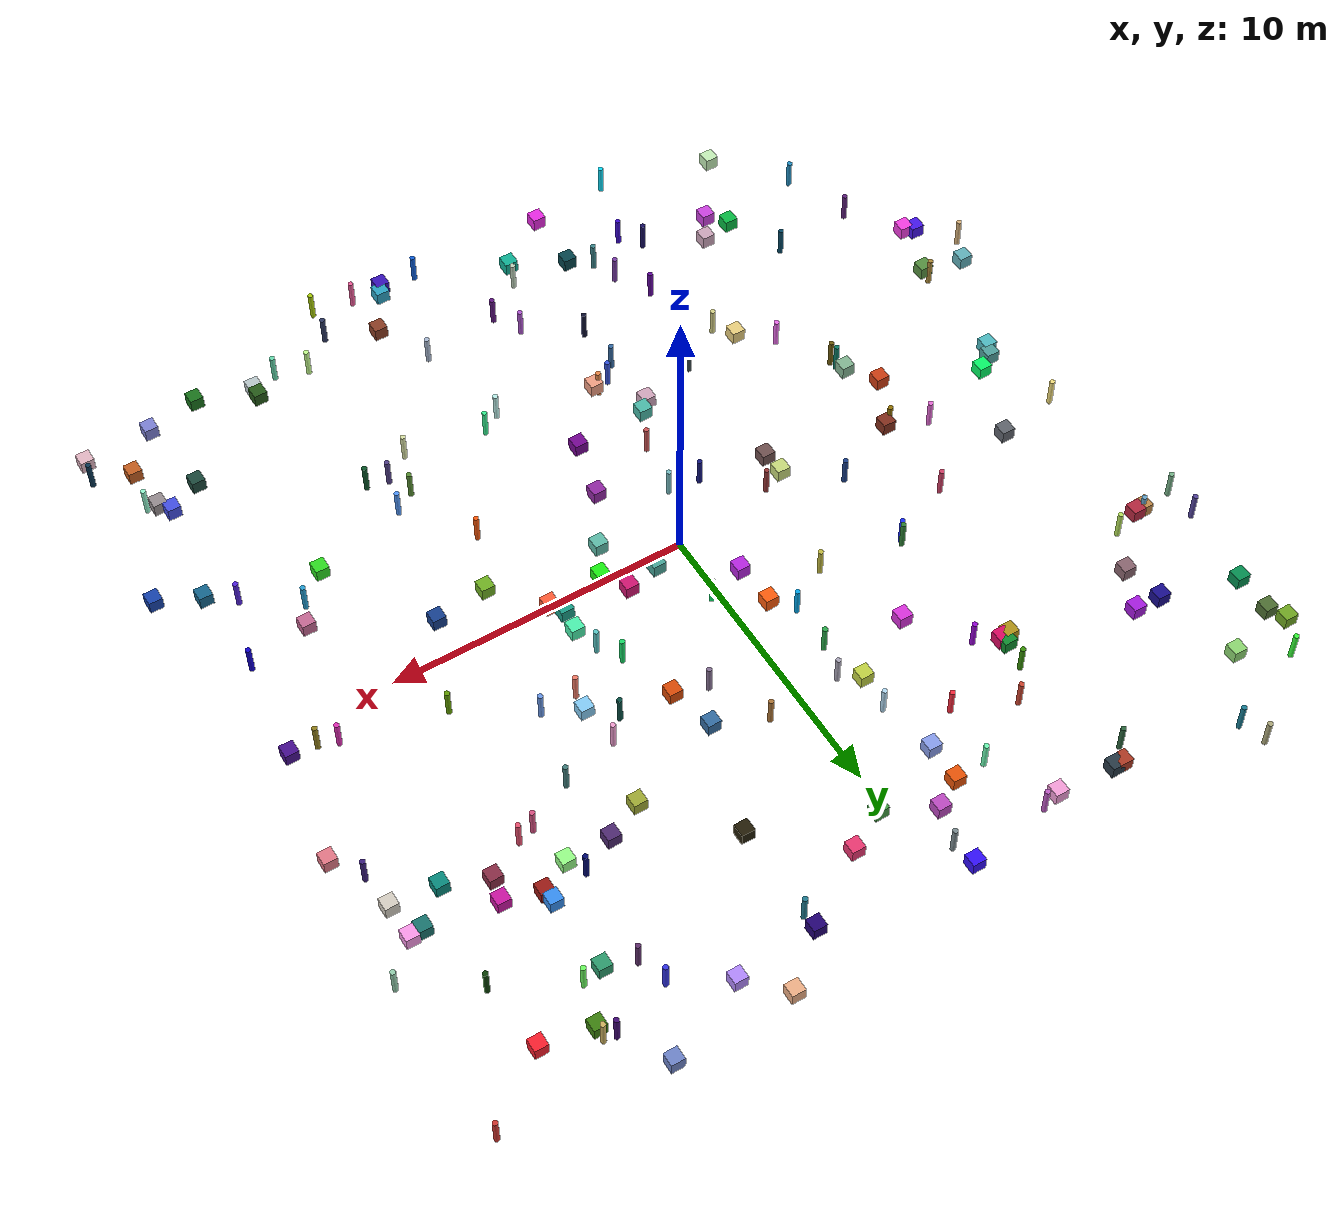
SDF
<sdf version="1.7">
 <world name="warehouse">
  <physics type="ode"><max_step_size>0.003</max_step_size><real_time_factor>1.0</real_time_factor></physics>
  <plugin name="ignition::gazebo::systems::Physics" filename="libignition-gazebo-physics-system.so"/>
  <plugin name="ignition::gazebo::systems::UserCommands" filename="libignition-gazebo-user-commands-system.so"/>
  <plugin name="ignition::gazebo::systems::SceneBroadcaster" filename="libignition-gazebo-scene-broadcaster-system.so"/>
  <plugin name="ignition::gazebo::systems::Sensors" filename="libignition-gazebo-sensors-system.so">
   <render_engine>ogre2</render_engine>
  </plugin>
  <plugin name="ignition::gazebo::systems::Imu" filename="libignition-gazebo-imu-system.so"/>
  <plugin name="ignition::gazebo::systems::NavSat" filename="libignition-gazebo-navsat-system.so"/>
  <scene>
   <ambient>1 1 1 1</ambient>
   <background>0 0 0 1</background>
   <shadows>0</shadows>
   <grid>false</grid>
  </scene>
  <spherical_coordinates>
   <surface_model>EARTH_WGS84</surface_model>
   <world_frame_orientation>ENU</world_frame_orientation>
   <latitude_deg>-22.986687</latitude_deg>
   <longitude_deg>-43.202501</longitude_deg>
   <elevation>0</elevation>
   <heading_deg>0</heading_deg>
  </spherical_coordinates>
  <model name="ground_plane">
   <static>true</static>
   <link name="link">
    <collision name="collision">
     <geometry><plane><normal>0.0 0.0 1</normal><size>1 1</size></plane></geometry>
    </collision>
   </link>
  </model>
  <model name="unit_box_0">
   <static>true</static>
   <pose>13.37 -5.86 0 0 0 0</pose>
   <link name="link">
    <collision name="collision">
     <geometry><box><size>0.450000 0.450000 0.450000</size></box></geometry>
    </collision>
    <visual name="visual">
     <geometry><box><size>0.450000 0.450000 0.450000</size></box></geometry>
     <material>
      <ambient>0.08826428566511146 0.4038599944238248 0.5587865503291078 1</ambient>
      <diffuse>0.08826428566511146 0.4038599944238248 0.5587865503291078 1</diffuse>
      <script><uri>file://media/materials/scripts/gazebo.material</uri><name>Gazebo/RandomColor0</name></script>
     </material>
    </visual>
   </link>
  </model>
  <model name="unit_cylinder_0">
   <static>true</static>
   <pose>-13.67 12.86 0 0 0 0</pose>
   <link name="link">
    <collision name="collision">
     <geometry><cylinder><radius>0.085000</radius><length>1.000000</length></cylinder></geometry>
    </collision>
    <visual name="visual">
     <geometry><cylinder><radius>0.085000</radius><length>1.000000</length></cylinder></geometry>
     <material>
      <ambient>0.22643290799938598 0.9941781518883074 0.23284495869942612 1</ambient>
      <diffuse>0.22643290799938598 0.9941781518883074 0.23284495869942612 1</diffuse>
      <script><uri>file://media/materials/scripts/gazebo.material</uri><name>Gazebo/RandomColor0</name></script>
     </material>
    </visual>
   </link>
  </model>
  <model name="unit_box_1">
   <static>true</static>
   <pose>-12.08 12.1 0 0 0 0</pose>
   <link name="link">
    <collision name="collision">
     <geometry><box><size>0.450000 0.450000 0.450000</size></box></geometry>
    </collision>
    <visual name="visual">
     <geometry><box><size>0.450000 0.450000 0.450000</size></box></geometry>
     <material>
      <ambient>0.5570859868462826 0.8457534030599224 0.4479570237474677 1</ambient>
      <diffuse>0.5570859868462826 0.8457534030599224 0.4479570237474677 1</diffuse>
      <script><uri>file://media/materials/scripts/gazebo.material</uri><name>Gazebo/RandomColor1</name></script>
     </material>
    </visual>
   </link>
  </model>
  <model name="unit_cylinder_1">
   <static>true</static>
   <pose>-6.13 3.12 0 0 0 0</pose>
   <link name="link">
    <collision name="collision">
     <geometry><cylinder><radius>0.085000</radius><length>1.000000</length></cylinder></geometry>
    </collision>
    <visual name="visual">
     <geometry><cylinder><radius>0.085000</radius><length>1.000000</length></cylinder></geometry>
     <material>
      <ambient>0.09784602003423482 0.17393467383219674 0.9556567217976356 1</ambient>
      <diffuse>0.09784602003423482 0.17393467383219674 0.9556567217976356 1</diffuse>
      <script><uri>file://media/materials/scripts/gazebo.material</uri><name>Gazebo/RandomColor1</name></script>
     </material>
    </visual>
   </link>
  </model>
  <model name="unit_box_2">
   <static>true</static>
   <pose>10.55 12.86 0 0 0 0</pose>
   <link name="link">
    <collision name="collision">
     <geometry><box><size>0.450000 0.450000 0.450000</size></box></geometry>
    </collision>
    <visual name="visual">
     <geometry><box><size>0.450000 0.450000 0.450000</size></box></geometry>
     <material>
      <ambient>0.23850958302615732 0.5061640008966156 0.061965873634879265 1</ambient>
      <diffuse>0.23850958302615732 0.5061640008966156 0.061965873634879265 1</diffuse>
      <script><uri>file://media/materials/scripts/gazebo.material</uri><name>Gazebo/RandomColor2</name></script>
     </material>
    </visual>
   </link>
  </model>
  <model name="unit_cylinder_2">
   <static>true</static>
   <pose>5.97 -6.44 0 0 0 0</pose>
   <link name="link">
    <collision name="collision">
     <geometry><cylinder><radius>0.085000</radius><length>1.000000</length></cylinder></geometry>
    </collision>
    <visual name="visual">
     <geometry><cylinder><radius>0.085000</radius><length>1.000000</length></cylinder></geometry>
     <material>
      <ambient>0.3449785465370162 0.561180177442619 0.20164393201053876 1</ambient>
      <diffuse>0.3449785465370162 0.561180177442619 0.20164393201053876 1</diffuse>
      <script><uri>file://media/materials/scripts/gazebo.material</uri><name>Gazebo/RandomColor2</name></script>
     </material>
    </visual>
   </link>
  </model>
  <model name="unit_box_3">
   <static>true</static>
   <pose>10.68 7.32 0 0 0 0</pose>
   <link name="link">
    <collision name="collision">
     <geometry><box><size>0.450000 0.450000 0.450000</size></box></geometry>
    </collision>
    <visual name="visual">
     <geometry><box><size>0.450000 0.450000 0.450000</size></box></geometry>
     <material>
      <ambient>0.5432476757430381 0.17729933388200625 0.28257987179646626 1</ambient>
      <diffuse>0.5432476757430381 0.17729933388200625 0.28257987179646626 1</diffuse>
      <script><uri>file://media/materials/scripts/gazebo.material</uri><name>Gazebo/RandomColor3</name></script>
     </material>
    </visual>
   </link>
  </model>
  <model name="unit_cylinder_3">
   <static>true</static>
   <pose>0.08 1.98 0 0 0 0</pose>
   <link name="link">
    <collision name="collision">
     <geometry><cylinder><radius>0.085000</radius><length>1.000000</length></cylinder></geometry>
    </collision>
    <visual name="visual">
     <geometry><cylinder><radius>0.085000</radius><length>1.000000</length></cylinder></geometry>
     <material>
      <ambient>0.060179974581356266 0.9140892420490736 0.43451321520392694 1</ambient>
      <diffuse>0.060179974581356266 0.9140892420490736 0.43451321520392694 1</diffuse>
      <script><uri>file://media/materials/scripts/gazebo.material</uri><name>Gazebo/RandomColor3</name></script>
     </material>
    </visual>
   </link>
  </model>
  <model name="unit_box_4">
   <static>true</static>
   <pose>13.61 6.59 0 0 0 0</pose>
   <link name="link">
    <collision name="collision">
     <geometry><box><size>0.450000 0.450000 0.450000</size></box></geometry>
    </collision>
    <visual name="visual">
     <geometry><box><size>0.450000 0.450000 0.450000</size></box></geometry>
     <material>
      <ambient>0.8401298544246089 0.8131445231318308 0.7653261206102966 1</ambient>
      <diffuse>0.8401298544246089 0.8131445231318308 0.7653261206102966 1</diffuse>
      <script><uri>file://media/materials/scripts/gazebo.material</uri><name>Gazebo/RandomColor4</name></script>
     </material>
    </visual>
   </link>
  </model>
  <model name="unit_cylinder_4">
   <static>true</static>
   <pose>4.72 4.29 0 0 0 0</pose>
   <link name="link">
    <collision name="collision">
     <geometry><cylinder><radius>0.085000</radius><length>1.000000</length></cylinder></geometry>
    </collision>
    <visual name="visual">
     <geometry><cylinder><radius>0.085000</radius><length>1.000000</length></cylinder></geometry>
     <material>
      <ambient>0.03826154303175866 0.310535022943797 0.2691551721576553 1</ambient>
      <diffuse>0.03826154303175866 0.310535022943797 0.2691551721576553 1</diffuse>
      <script><uri>file://media/materials/scripts/gazebo.material</uri><name>Gazebo/RandomColor4</name></script>
     </material>
    </visual>
   </link>
  </model>
  <model name="unit_box_5">
   <static>true</static>
   <pose>9.89 -4.94 0 0 0 0</pose>
   <link name="link">
    <collision name="collision">
     <geometry><box><size>0.450000 0.450000 0.450000</size></box></geometry>
    </collision>
    <visual name="visual">
     <geometry><box><size>0.450000 0.450000 0.450000</size></box></geometry>
     <material>
      <ambient>0.18305160549795496 0.8707921544052755 0.13400563533214793 1</ambient>
      <diffuse>0.18305160549795496 0.8707921544052755 0.13400563533214793 1</diffuse>
      <script><uri>file://media/materials/scripts/gazebo.material</uri><name>Gazebo/RandomColor5</name></script>
     </material>
    </visual>
   </link>
  </model>
  <model name="unit_cylinder_5">
   <static>true</static>
   <pose>-1.19 -6.96 0 0 0 0</pose>
   <link name="link">
    <collision name="collision">
     <geometry><cylinder><radius>0.085000</radius><length>1.000000</length></cylinder></geometry>
    </collision>
    <visual name="visual">
     <geometry><cylinder><radius>0.085000</radius><length>1.000000</length></cylinder></geometry>
     <material>
      <ambient>0.9185062840085724 0.5292186607881189 0.28162312539047907 1</ambient>
      <diffuse>0.9185062840085724 0.5292186607881189 0.28162312539047907 1</diffuse>
      <script><uri>file://media/materials/scripts/gazebo.material</uri><name>Gazebo/RandomColor5</name></script>
     </material>
    </visual>
   </link>
  </model>
  <model name="unit_box_6">
   <static>true</static>
   <pose>14.4 4.38 0 0 0 0</pose>
   <link name="link">
    <collision name="collision">
     <geometry><box><size>0.450000 0.450000 0.450000</size></box></geometry>
    </collision>
    <visual name="visual">
     <geometry><box><size>0.450000 0.450000 0.450000</size></box></geometry>
     <material>
      <ambient>0.8923392405059082 0.470771838638417 0.5278958681375123 1</ambient>
      <diffuse>0.8923392405059082 0.470771838638417 0.5278958681375123 1</diffuse>
      <script><uri>file://media/materials/scripts/gazebo.material</uri><name>Gazebo/RandomColor6</name></script>
     </material>
    </visual>
   </link>
  </model>
  <model name="unit_cylinder_6">
   <static>true</static>
   <pose>-4.87 -9.81 0 0 0 0</pose>
   <link name="link">
    <collision name="collision">
     <geometry><cylinder><radius>0.085000</radius><length>1.000000</length></cylinder></geometry>
    </collision>
    <visual name="visual">
     <geometry><cylinder><radius>0.085000</radius><length>1.000000</length></cylinder></geometry>
     <material>
      <ambient>0.38331743552222297 0.027572329405924578 0.6235658209803379 1</ambient>
      <diffuse>0.38331743552222297 0.027572329405924578 0.6235658209803379 1</diffuse>
      <script><uri>file://media/materials/scripts/gazebo.material</uri><name>Gazebo/RandomColor6</name></script>
     </material>
    </visual>
   </link>
  </model>
  <model name="unit_box_7">
   <static>true</static>
   <pose>-8.14 -0.72 0 0 0 0</pose>
   <link name="link">
    <collision name="collision">
     <geometry><box><size>0.450000 0.450000 0.450000</size></box></geometry>
    </collision>
    <visual name="visual">
     <geometry><box><size>0.450000 0.450000 0.450000</size></box></geometry>
     <material>
      <ambient>0.5168723721213653 0.18612557674347563 0.11343065469603886 1</ambient>
      <diffuse>0.5168723721213653 0.18612557674347563 0.11343065469603886 1</diffuse>
      <script><uri>file://media/materials/scripts/gazebo.material</uri><name>Gazebo/RandomColor7</name></script>
     </material>
    </visual>
   </link>
  </model>
  <model name="unit_cylinder_7">
   <static>true</static>
   <pose>8.26 8.36 0 0 0 0</pose>
   <link name="link">
    <collision name="collision">
     <geometry><cylinder><radius>0.085000</radius><length>1.000000</length></cylinder></geometry>
    </collision>
    <visual name="visual">
     <geometry><cylinder><radius>0.085000</radius><length>1.000000</length></cylinder></geometry>
     <material>
      <ambient>0.010536000804149181 0.039938422784112415 0.44365025666165325 1</ambient>
      <diffuse>0.010536000804149181 0.039938422784112415 0.44365025666165325 1</diffuse>
      <script><uri>file://media/materials/scripts/gazebo.material</uri><name>Gazebo/RandomColor7</name></script>
     </material>
    </visual>
   </link>
  </model>
  <model name="unit_box_8">
   <static>true</static>
   <pose>9.6 8.85 0 0 0 0</pose>
   <link name="link">
    <collision name="collision">
     <geometry><box><size>0.450000 0.450000 0.450000</size></box></geometry>
    </collision>
    <visual name="visual">
     <geometry><box><size>0.450000 0.450000 0.450000</size></box></geometry>
     <material>
      <ambient>0.21281683753546676 0.5594621285025635 0.9515530543112825 1</ambient>
      <diffuse>0.21281683753546676 0.5594621285025635 0.9515530543112825 1</diffuse>
      <script><uri>file://media/materials/scripts/gazebo.material</uri><name>Gazebo/RandomColor8</name></script>
     </material>
    </visual>
   </link>
  </model>
  <model name="unit_cylinder_8">
   <static>true</static>
   <pose>-7.27 -5.82 0 0 0 0</pose>
   <link name="link">
    <collision name="collision">
     <geometry><cylinder><radius>0.085000</radius><length>1.000000</length></cylinder></geometry>
    </collision>
    <visual name="visual">
     <geometry><cylinder><radius>0.085000</radius><length>1.000000</length></cylinder></geometry>
     <material>
      <ambient>0.9273169458376869 0.42573511504897754 0.9271410663157754 1</ambient>
      <diffuse>0.9273169458376869 0.42573511504897754 0.9271410663157754 1</diffuse>
      <script><uri>file://media/materials/scripts/gazebo.material</uri><name>Gazebo/RandomColor8</name></script>
     </material>
    </visual>
   </link>
  </model>
  <model name="unit_box_9">
   <static>true</static>
   <pose>5.4 14.78 0 0 0 0</pose>
   <link name="link">
    <collision name="collision">
     <geometry><box><size>0.450000 0.450000 0.450000</size></box></geometry>
    </collision>
    <visual name="visual">
     <geometry><box><size>0.450000 0.450000 0.450000</size></box></geometry>
     <material>
      <ambient>0.9377994021996059 0.6914780809308397 0.5269026652407088 1</ambient>
      <diffuse>0.9377994021996059 0.6914780809308397 0.5269026652407088 1</diffuse>
      <script><uri>file://media/materials/scripts/gazebo.material</uri><name>Gazebo/RandomColor9</name></script>
     </material>
    </visual>
   </link>
  </model>
  <model name="unit_cylinder_9">
   <static>true</static>
   <pose>-1.0 -2.29 0 0 0 0</pose>
   <link name="link">
    <collision name="collision">
     <geometry><cylinder><radius>0.085000</radius><length>1.000000</length></cylinder></geometry>
    </collision>
    <visual name="visual">
     <geometry><cylinder><radius>0.085000</radius><length>1.000000</length></cylinder></geometry>
     <material>
      <ambient>0.47917200845864116 0.7596924477369887 0.7812414801510158 1</ambient>
      <diffuse>0.47917200845864116 0.7596924477369887 0.7812414801510158 1</diffuse>
      <script><uri>file://media/materials/scripts/gazebo.material</uri><name>Gazebo/RandomColor9</name></script>
     </material>
    </visual>
   </link>
  </model>
  <model name="unit_box_10">
   <static>true</static>
   <pose>0.16 11.13 0 0 0 0</pose>
   <link name="link">
    <collision name="collision">
     <geometry><box><size>0.450000 0.450000 0.450000</size></box></geometry>
    </collision>
    <visual name="visual">
     <geometry><box><size>0.450000 0.450000 0.450000</size></box></geometry>
     <material>
      <ambient>0.25730476471138275 0.6113861432114318 0.26210039634027194 1</ambient>
      <diffuse>0.25730476471138275 0.6113861432114318 0.26210039634027194 1</diffuse>
      <script><uri>file://media/materials/scripts/gazebo.material</uri><name>Gazebo/RandomColor10</name></script>
     </material>
    </visual>
   </link>
  </model>
  <model name="unit_cylinder_10">
   <static>true</static>
   <pose>9.38 6.47 0 0 0 0</pose>
   <link name="link">
    <collision name="collision">
     <geometry><cylinder><radius>0.085000</radius><length>1.000000</length></cylinder></geometry>
    </collision>
    <visual name="visual">
     <geometry><cylinder><radius>0.085000</radius><length>1.000000</length></cylinder></geometry>
     <material>
      <ambient>0.9181208071983159 0.3168006436108135 0.4392921452807552 1</ambient>
      <diffuse>0.9181208071983159 0.3168006436108135 0.4392921452807552 1</diffuse>
      <script><uri>file://media/materials/scripts/gazebo.material</uri><name>Gazebo/RandomColor10</name></script>
     </material>
    </visual>
   </link>
  </model>
  <model name="unit_box_11">
   <static>true</static>
   <pose>-11.18 1.52 0 0 0 0</pose>
   <link name="link">
    <collision name="collision">
     <geometry><box><size>0.450000 0.450000 0.450000</size></box></geometry>
    </collision>
    <visual name="visual">
     <geometry><box><size>0.450000 0.450000 0.450000</size></box></geometry>
     <material>
      <ambient>0.37673299942862404 0.3952141431706322 0.4295230742137489 1</ambient>
      <diffuse>0.37673299942862404 0.3952141431706322 0.4295230742137489 1</diffuse>
      <script><uri>file://media/materials/scripts/gazebo.material</uri><name>Gazebo/RandomColor11</name></script>
     </material>
    </visual>
   </link>
  </model>
  <model name="unit_cylinder_11">
   <static>true</static>
   <pose>5.42 -7.89 0 0 0 0</pose>
   <link name="link">
    <collision name="collision">
     <geometry><cylinder><radius>0.085000</radius><length>1.000000</length></cylinder></geometry>
    </collision>
    <visual name="visual">
     <geometry><cylinder><radius>0.085000</radius><length>1.000000</length></cylinder></geometry>
     <material>
      <ambient>0.8632042588659117 0.8958915272058344 0.6608747969953866 1</ambient>
      <diffuse>0.8632042588659117 0.8958915272058344 0.6608747969953866 1</diffuse>
      <script><uri>file://media/materials/scripts/gazebo.material</uri><name>Gazebo/RandomColor11</name></script>
     </material>
    </visual>
   </link>
  </model>
  <model name="unit_box_12">
   <static>true</static>
   <pose>0.66 -5.08 0 0 0 0</pose>
   <link name="link">
    <collision name="collision">
     <geometry><box><size>0.450000 0.450000 0.450000</size></box></geometry>
    </collision>
    <visual name="visual">
     <geometry><box><size>0.450000 0.450000 0.450000</size></box></geometry>
     <material>
      <ambient>0.45986079268229807 0.023242793074265022 0.5792352809576616 1</ambient>
      <diffuse>0.45986079268229807 0.023242793074265022 0.5792352809576616 1</diffuse>
      <script><uri>file://media/materials/scripts/gazebo.material</uri><name>Gazebo/RandomColor12</name></script>
     </material>
    </visual>
   </link>
  </model>
  <model name="unit_cylinder_12">
   <static>true</static>
   <pose>-1.89 3.71 0 0 0 0</pose>
   <link name="link">
    <collision name="collision">
     <geometry><cylinder><radius>0.085000</radius><length>1.000000</length></cylinder></geometry>
    </collision>
    <visual name="visual">
     <geometry><cylinder><radius>0.085000</radius><length>1.000000</length></cylinder></geometry>
     <material>
      <ambient>0.012275883180770775 0.6622361219837193 0.9321971385392855 1</ambient>
      <diffuse>0.012275883180770775 0.6622361219837193 0.9321971385392855 1</diffuse>
      <script><uri>file://media/materials/scripts/gazebo.material</uri><name>Gazebo/RandomColor12</name></script>
     </material>
    </visual>
   </link>
  </model>
  <model name="unit_box_13">
   <static>true</static>
   <pose>8.38 -12.26 0 0 0 0</pose>
   <link name="link">
    <collision name="collision">
     <geometry><box><size>0.450000 0.450000 0.450000</size></box></geometry>
    </collision>
    <visual name="visual">
     <geometry><box><size>0.450000 0.450000 0.450000</size></box></geometry>
     <material>
      <ambient>0.1477417695941674 0.3519265693878383 0.09713290157866372 1</ambient>
      <diffuse>0.1477417695941674 0.3519265693878383 0.09713290157866372 1</diffuse>
      <script><uri>file://media/materials/scripts/gazebo.material</uri><name>Gazebo/RandomColor13</name></script>
     </material>
    </visual>
   </link>
  </model>
  <model name="unit_cylinder_13">
   <static>true</static>
   <pose>13.69 5.23 0 0 0 0</pose>
   <link name="link">
    <collision name="collision">
     <geometry><cylinder><radius>0.085000</radius><length>1.000000</length></cylinder></geometry>
    </collision>
    <visual name="visual">
     <geometry><cylinder><radius>0.085000</radius><length>1.000000</length></cylinder></geometry>
     <material>
      <ambient>0.23840866738330357 0.12341911439382347 0.4981785556465306 1</ambient>
      <diffuse>0.23840866738330357 0.12341911439382347 0.4981785556465306 1</diffuse>
      <script><uri>file://media/materials/scripts/gazebo.material</uri><name>Gazebo/RandomColor13</name></script>
     </material>
    </visual>
   </link>
  </model>
  <model name="unit_box_14">
   <static>true</static>
   <pose>-8.61 -10.91 0 0 0 0</pose>
   <link name="link">
    <collision name="collision">
     <geometry><box><size>0.450000 0.450000 0.450000</size></box></geometry>
    </collision>
    <visual name="visual">
     <geometry><box><size>0.450000 0.450000 0.450000</size></box></geometry>
     <material>
      <ambient>0.03165804897786417 0.729032787102438 0.2672408092221674 1</ambient>
      <diffuse>0.03165804897786417 0.729032787102438 0.2672408092221674 1</diffuse>
      <script><uri>file://media/materials/scripts/gazebo.material</uri><name>Gazebo/RandomColor14</name></script>
     </material>
    </visual>
   </link>
  </model>
  <model name="unit_cylinder_14">
   <static>true</static>
   <pose>13.32 -10.17 0 0 0 0</pose>
   <link name="link">
    <collision name="collision">
     <geometry><cylinder><radius>0.085000</radius><length>1.000000</length></cylinder></geometry>
    </collision>
    <visual name="visual">
     <geometry><cylinder><radius>0.085000</radius><length>1.000000</length></cylinder></geometry>
     <material>
      <ambient>0.5847449927546251 0.9795083278853924 0.8247499233290505 1</ambient>
      <diffuse>0.5847449927546251 0.9795083278853924 0.8247499233290505 1</diffuse>
      <script><uri>file://media/materials/scripts/gazebo.material</uri><name>Gazebo/RandomColor14</name></script>
     </material>
    </visual>
   </link>
  </model>
  <model name="unit_box_15">
   <static>true</static>
   <pose>3.07 4.57 0 0 0 0</pose>
   <link name="link">
    <collision name="collision">
     <geometry><box><size>0.450000 0.450000 0.450000</size></box></geometry>
    </collision>
    <visual name="visual">
     <geometry><box><size>0.450000 0.450000 0.450000</size></box></geometry>
     <material>
      <ambient>0.8661199399045274 0.29588432611453774 0.029544778753045176 1</ambient>
      <diffuse>0.8661199399045274 0.29588432611453774 0.029544778753045176 1</diffuse>
      <script><uri>file://media/materials/scripts/gazebo.material</uri><name>Gazebo/RandomColor15</name></script>
     </material>
    </visual>
   </link>
  </model>
  <model name="unit_cylinder_15">
   <static>true</static>
   <pose>10.52 13.14 0 0 0 0</pose>
   <link name="link">
    <collision name="collision">
     <geometry><cylinder><radius>0.085000</radius><length>1.000000</length></cylinder></geometry>
    </collision>
    <visual name="visual">
     <geometry><cylinder><radius>0.085000</radius><length>1.000000</length></cylinder></geometry>
     <material>
      <ambient>0.8126317924130658 0.7037773503482371 0.380102691503139 1</ambient>
      <diffuse>0.8126317924130658 0.7037773503482371 0.380102691503139 1</diffuse>
      <script><uri>file://media/materials/scripts/gazebo.material</uri><name>Gazebo/RandomColor15</name></script>
     </material>
    </visual>
   </link>
  </model>
  <model name="unit_box_16">
   <static>true</static>
   <pose>-1.03 -6.97 0 0 0 0</pose>
   <link name="link">
    <collision name="collision">
     <geometry><box><size>0.450000 0.450000 0.450000</size></box></geometry>
    </collision>
    <visual name="visual">
     <geometry><box><size>0.450000 0.450000 0.450000</size></box></geometry>
     <material>
      <ambient>0.947777378717247 0.6242593842534916 0.5180780460162824 1</ambient>
      <diffuse>0.947777378717247 0.6242593842534916 0.5180780460162824 1</diffuse>
      <script><uri>file://media/materials/scripts/gazebo.material</uri><name>Gazebo/RandomColor16</name></script>
     </material>
    </visual>
   </link>
  </model>
  <model name="unit_cylinder_16">
   <static>true</static>
   <pose>-2.09 8.08 0 0 0 0</pose>
   <link name="link">
    <collision name="collision">
     <geometry><cylinder><radius>0.085000</radius><length>1.000000</length></cylinder></geometry>
    </collision>
    <visual name="visual">
     <geometry><cylinder><radius>0.085000</radius><length>1.000000</length></cylinder></geometry>
     <material>
      <ambient>0.7019170491834359 0.8626682858190757 0.9624429712199282 1</ambient>
      <diffuse>0.7019170491834359 0.8626682858190757 0.9624429712199282 1</diffuse>
      <script><uri>file://media/materials/scripts/gazebo.material</uri><name>Gazebo/RandomColor16</name></script>
     </material>
    </visual>
   </link>
  </model>
  <model name="unit_box_17">
   <static>true</static>
   <pose>-4.24 -0.88 0 0 0 0</pose>
   <link name="link">
    <collision name="collision">
     <geometry><box><size>0.450000 0.450000 0.450000</size></box></geometry>
    </collision>
    <visual name="visual">
     <geometry><box><size>0.450000 0.450000 0.450000</size></box></geometry>
     <material>
      <ambient>0.7868893250944816 0.8572085940770652 0.4870029069797954 1</ambient>
      <diffuse>0.7868893250944816 0.8572085940770652 0.4870029069797954 1</diffuse>
      <script><uri>file://media/materials/scripts/gazebo.material</uri><name>Gazebo/RandomColor17</name></script>
     </material>
    </visual>
   </link>
  </model>
  <model name="unit_cylinder_17">
   <static>true</static>
   <pose>-3.52 11.22 0 0 0 0</pose>
   <link name="link">
    <collision name="collision">
     <geometry><cylinder><radius>0.085000</radius><length>1.000000</length></cylinder></geometry>
    </collision>
    <visual name="visual">
     <geometry><cylinder><radius>0.085000</radius><length>1.000000</length></cylinder></geometry>
     <material>
      <ambient>0.4379534641081445 0.9886863089113719 0.7163692880442633 1</ambient>
      <diffuse>0.4379534641081445 0.9886863089113719 0.7163692880442633 1</diffuse>
      <script><uri>file://media/materials/scripts/gazebo.material</uri><name>Gazebo/RandomColor17</name></script>
     </material>
    </visual>
   </link>
  </model>
  <model name="unit_box_18">
   <static>true</static>
   <pose>-8.09 -11.53 0 0 0 0</pose>
   <link name="link">
    <collision name="collision">
     <geometry><box><size>0.450000 0.450000 0.450000</size></box></geometry>
    </collision>
    <visual name="visual">
     <geometry><box><size>0.450000 0.450000 0.450000</size></box></geometry>
     <material>
      <ambient>0.803963229090372 0.2652458061627242 0.8816610414404282 1</ambient>
      <diffuse>0.803963229090372 0.2652458061627242 0.8816610414404282 1</diffuse>
      <script><uri>file://media/materials/scripts/gazebo.material</uri><name>Gazebo/RandomColor18</name></script>
     </material>
    </visual>
   </link>
  </model>
  <model name="unit_cylinder_18">
   <static>true</static>
   <pose>2.74 -7.41 0 0 0 0</pose>
   <link name="link">
    <collision name="collision">
     <geometry><cylinder><radius>0.085000</radius><length>1.000000</length></cylinder></geometry>
    </collision>
    <visual name="visual">
     <geometry><cylinder><radius>0.085000</radius><length>1.000000</length></cylinder></geometry>
     <material>
      <ambient>0.22363109058887753 0.9558468197445318 0.5860861934914426 1</ambient>
      <diffuse>0.22363109058887753 0.9558468197445318 0.5860861934914426 1</diffuse>
      <script><uri>file://media/materials/scripts/gazebo.material</uri><name>Gazebo/RandomColor18</name></script>
     </material>
    </visual>
   </link>
  </model>
  <model name="unit_box_19">
   <static>true</static>
   <pose>-12.84 -1.78 0 0 0 0</pose>
   <link name="link">
    <collision name="collision">
     <geometry><box><size>0.450000 0.450000 0.450000</size></box></geometry>
    </collision>
    <visual name="visual">
     <geometry><box><size>0.450000 0.450000 0.450000</size></box></geometry>
     <material>
      <ambient>0.3059121022247705 0.7342512263007779 0.7647108240388901 1</ambient>
      <diffuse>0.3059121022247705 0.7342512263007779 0.7647108240388901 1</diffuse>
      <script><uri>file://media/materials/scripts/gazebo.material</uri><name>Gazebo/RandomColor19</name></script>
     </material>
    </visual>
   </link>
  </model>
  <model name="unit_cylinder_19">
   <static>true</static>
   <pose>-14.41 7.07 0 0 0 0</pose>
   <link name="link">
    <collision name="collision">
     <geometry><cylinder><radius>0.085000</radius><length>1.000000</length></cylinder></geometry>
    </collision>
    <visual name="visual">
     <geometry><cylinder><radius>0.085000</radius><length>1.000000</length></cylinder></geometry>
     <material>
      <ambient>0.33439763254681787 0.27544390366701443 0.6192885381677653 1</ambient>
      <diffuse>0.33439763254681787 0.27544390366701443 0.6192885381677653 1</diffuse>
      <script><uri>file://media/materials/scripts/gazebo.material</uri><name>Gazebo/RandomColor19</name></script>
     </material>
    </visual>
   </link>
  </model>
  <model name="unit_box_20">
   <static>true</static>
   <pose>-6.79 13.47 0 0 0 0</pose>
   <link name="link">
    <collision name="collision">
     <geometry><box><size>0.450000 0.450000 0.450000</size></box></geometry>
    </collision>
    <visual name="visual">
     <geometry><box><size>0.450000 0.450000 0.450000</size></box></geometry>
     <material>
      <ambient>0.6862984897451937 0.23210744080559476 0.14412165187279047 1</ambient>
      <diffuse>0.6862984897451937 0.23210744080559476 0.14412165187279047 1</diffuse>
      <script><uri>file://media/materials/scripts/gazebo.material</uri><name>Gazebo/RandomColor20</name></script>
     </material>
    </visual>
   </link>
  </model>
  <model name="unit_cylinder_20">
   <static>true</static>
   <pose>12.8 0.52 0 0 0 0</pose>
   <link name="link">
    <collision name="collision">
     <geometry><cylinder><radius>0.085000</radius><length>1.000000</length></cylinder></geometry>
    </collision>
    <visual name="visual">
     <geometry><cylinder><radius>0.085000</radius><length>1.000000</length></cylinder></geometry>
     <material>
      <ambient>0.5755740909761914 0.507086843042378 0.11988730785576618 1</ambient>
      <diffuse>0.5755740909761914 0.507086843042378 0.11988730785576618 1</diffuse>
      <script><uri>file://media/materials/scripts/gazebo.material</uri><name>Gazebo/RandomColor20</name></script>
     </material>
    </visual>
   </link>
  </model>
  <model name="unit_box_21">
   <static>true</static>
   <pose>8.37 -12.6 0 0 0 0</pose>
   <link name="link">
    <collision name="collision">
     <geometry><box><size>0.450000 0.450000 0.450000</size></box></geometry>
    </collision>
    <visual name="visual">
     <geometry><box><size>0.450000 0.450000 0.450000</size></box></geometry>
     <material>
      <ambient>0.7326866111408485 0.7859811385692107 0.8015302505751346 1</ambient>
      <diffuse>0.7326866111408485 0.7859811385692107 0.8015302505751346 1</diffuse>
      <script><uri>file://media/materials/scripts/gazebo.material</uri><name>Gazebo/RandomColor21</name></script>
     </material>
    </visual>
   </link>
  </model>
  <model name="unit_cylinder_21">
   <static>true</static>
   <pose>-8.35 -3.89 0 0 0 0</pose>
   <link name="link">
    <collision name="collision">
     <geometry><cylinder><radius>0.085000</radius><length>1.000000</length></cylinder></geometry>
    </collision>
    <visual name="visual">
     <geometry><cylinder><radius>0.085000</radius><length>1.000000</length></cylinder></geometry>
     <material>
      <ambient>0.037104033649876356 0.486294414116082 0.3978003462148725 1</ambient>
      <diffuse>0.037104033649876356 0.486294414116082 0.3978003462148725 1</diffuse>
      <script><uri>file://media/materials/scripts/gazebo.material</uri><name>Gazebo/RandomColor21</name></script>
     </material>
    </visual>
   </link>
  </model>
  <model name="unit_box_22">
   <static>true</static>
   <pose>-7.57 -10.68 0 0 0 0</pose>
   <link name="link">
    <collision name="collision">
     <geometry><box><size>0.450000 0.450000 0.450000</size></box></geometry>
    </collision>
    <visual name="visual">
     <geometry><box><size>0.450000 0.450000 0.450000</size></box></geometry>
     <material>
      <ambient>0.8056660260705587 0.651666072899554 0.7358513164409488 1</ambient>
      <diffuse>0.8056660260705587 0.651666072899554 0.7358513164409488 1</diffuse>
      <script><uri>file://media/materials/scripts/gazebo.material</uri><name>Gazebo/RandomColor22</name></script>
     </material>
    </visual>
   </link>
  </model>
  <model name="unit_cylinder_22">
   <static>true</static>
   <pose>2.11 -7.83 0 0 0 0</pose>
   <link name="link">
    <collision name="collision">
     <geometry><cylinder><radius>0.085000</radius><length>1.000000</length></cylinder></geometry>
    </collision>
    <visual name="visual">
     <geometry><cylinder><radius>0.085000</radius><length>1.000000</length></cylinder></geometry>
     <material>
      <ambient>0.7419928742520082 0.9435154976415809 0.9250426376935831 1</ambient>
      <diffuse>0.7419928742520082 0.9435154976415809 0.9250426376935831 1</diffuse>
      <script><uri>file://media/materials/scripts/gazebo.material</uri><name>Gazebo/RandomColor22</name></script>
     </material>
    </visual>
   </link>
  </model>
  <model name="unit_box_23">
   <static>true</static>
   <pose>-3.12 -14.37 0 0 0 0</pose>
   <link name="link">
    <collision name="collision">
     <geometry><box><size>0.450000 0.450000 0.450000</size></box></geometry>
    </collision>
    <visual name="visual">
     <geometry><box><size>0.450000 0.450000 0.450000</size></box></geometry>
     <material>
      <ambient>0.918416578895126 0.16488205674642376 0.8958546925203331 1</ambient>
      <diffuse>0.918416578895126 0.16488205674642376 0.8958546925203331 1</diffuse>
      <script><uri>file://media/materials/scripts/gazebo.material</uri><name>Gazebo/RandomColor23</name></script>
     </material>
    </visual>
   </link>
  </model>
  <model name="unit_cylinder_23">
   <static>true</static>
   <pose>5.43 2.92 0 0 0 0</pose>
   <link name="link">
    <collision name="collision">
     <geometry><cylinder><radius>0.085000</radius><length>1.000000</length></cylinder></geometry>
    </collision>
    <visual name="visual">
     <geometry><cylinder><radius>0.085000</radius><length>1.000000</length></cylinder></geometry>
     <material>
      <ambient>0.9478658710452448 0.4894878169720396 0.4094010127505088 1</ambient>
      <diffuse>0.9478658710452448 0.4894878169720396 0.4094010127505088 1</diffuse>
      <script><uri>file://media/materials/scripts/gazebo.material</uri><name>Gazebo/RandomColor23</name></script>
     </material>
    </visual>
   </link>
  </model>
  <model name="unit_box_24">
   <static>true</static>
   <pose>-4.58 13.34 0 0 0 0</pose>
   <link name="link">
    <collision name="collision">
     <geometry><box><size>0.450000 0.450000 0.450000</size></box></geometry>
    </collision>
    <visual name="visual">
     <geometry><box><size>0.450000 0.450000 0.450000</size></box></geometry>
     <material>
      <ambient>0.9587381781678423 0.6205069236833495 0.8506780297745122 1</ambient>
      <diffuse>0.9587381781678423 0.6205069236833495 0.8506780297745122 1</diffuse>
      <script><uri>file://media/materials/scripts/gazebo.material</uri><name>Gazebo/RandomColor24</name></script>
     </material>
    </visual>
   </link>
  </model>
  <model name="unit_cylinder_24">
   <static>true</static>
   <pose>-3.76 9.17 0 0 0 0</pose>
   <link name="link">
    <collision name="collision">
     <geometry><cylinder><radius>0.085000</radius><length>1.000000</length></cylinder></geometry>
    </collision>
    <visual name="visual">
     <geometry><cylinder><radius>0.085000</radius><length>1.000000</length></cylinder></geometry>
     <material>
      <ambient>0.9765241044740991 0.17076668221313585 0.2479138787878924 1</ambient>
      <diffuse>0.9765241044740991 0.17076668221313585 0.2479138787878924 1</diffuse>
      <script><uri>file://media/materials/scripts/gazebo.material</uri><name>Gazebo/RandomColor24</name></script>
     </material>
    </visual>
   </link>
  </model>
  <model name="unit_box_25">
   <static>true</static>
   <pose>-3.07 -12.2 0 0 0 0</pose>
   <link name="link">
    <collision name="collision">
     <geometry><box><size>0.450000 0.450000 0.450000</size></box></geometry>
    </collision>
    <visual name="visual">
     <geometry><box><size>0.450000 0.450000 0.450000</size></box></geometry>
     <material>
      <ambient>0.022567803826378685 0.27193777757583926 0.30225701377346936 1</ambient>
      <diffuse>0.022567803826378685 0.27193777757583926 0.30225701377346936 1</diffuse>
      <script><uri>file://media/materials/scripts/gazebo.material</uri><name>Gazebo/RandomColor25</name></script>
     </material>
    </visual>
   </link>
  </model>
  <model name="unit_cylinder_25">
   <static>true</static>
   <pose>12.2 0.75 0 0 0 0</pose>
   <link name="link">
    <collision name="collision">
     <geometry><cylinder><radius>0.085000</radius><length>1.000000</length></cylinder></geometry>
    </collision>
    <visual name="visual">
     <geometry><cylinder><radius>0.085000</radius><length>1.000000</length></cylinder></geometry>
     <material>
      <ambient>0.8865542128697605 0.18408492666172915 0.717390722208998 1</ambient>
      <diffuse>0.8865542128697605 0.18408492666172915 0.717390722208998 1</diffuse>
      <script><uri>file://media/materials/scripts/gazebo.material</uri><name>Gazebo/RandomColor25</name></script>
     </material>
    </visual>
   </link>
  </model>
  <model name="unit_box_26">
   <static>true</static>
   <pose>10.22 -13.13 0 0 0 0</pose>
   <link name="link">
    <collision name="collision">
     <geometry><box><size>0.450000 0.450000 0.450000</size></box></geometry>
    </collision>
    <visual name="visual">
     <geometry><box><size>0.450000 0.450000 0.450000</size></box></geometry>
     <material>
      <ambient>0.10199247166240621 0.4547971933936775 0.11272263631989154 1</ambient>
      <diffuse>0.10199247166240621 0.4547971933936775 0.11272263631989154 1</diffuse>
      <script><uri>file://media/materials/scripts/gazebo.material</uri><name>Gazebo/RandomColor26</name></script>
     </material>
    </visual>
   </link>
  </model>
  <model name="unit_cylinder_26">
   <static>true</static>
   <pose>0.96 6.66 0 0 0 0</pose>
   <link name="link">
    <collision name="collision">
     <geometry><cylinder><radius>0.085000</radius><length>1.000000</length></cylinder></geometry>
    </collision>
    <visual name="visual">
     <geometry><cylinder><radius>0.085000</radius><length>1.000000</length></cylinder></geometry>
     <material>
      <ambient>0.686953396201328 0.4656829672532363 0.2211493216272601 1</ambient>
      <diffuse>0.686953396201328 0.4656829672532363 0.2211493216272601 1</diffuse>
      <script><uri>file://media/materials/scripts/gazebo.material</uri><name>Gazebo/RandomColor26</name></script>
     </material>
    </visual>
   </link>
  </model>
  <model name="unit_box_27">
   <static>true</static>
   <pose>2.14 -1.31 0 0 0 0</pose>
   <link name="link">
    <collision name="collision">
     <geometry><box><size>0.450000 0.450000 0.450000</size></box></geometry>
    </collision>
    <visual name="visual">
     <geometry><box><size>0.450000 0.450000 0.450000</size></box></geometry>
     <material>
      <ambient>0.37025055253567474 0.7417899858536134 0.6649591891728481 1</ambient>
      <diffuse>0.37025055253567474 0.7417899858536134 0.6649591891728481 1</diffuse>
      <script><uri>file://media/materials/scripts/gazebo.material</uri><name>Gazebo/RandomColor27</name></script>
     </material>
    </visual>
   </link>
  </model>
  <model name="unit_cylinder_27">
   <static>true</static>
   <pose>-4.1 13.41 0 0 0 0</pose>
   <link name="link">
    <collision name="collision">
     <geometry><cylinder><radius>0.085000</radius><length>1.000000</length></cylinder></geometry>
    </collision>
    <visual name="visual">
     <geometry><cylinder><radius>0.085000</radius><length>1.000000</length></cylinder></geometry>
     <material>
      <ambient>0.763955425483993 0.36652504070580116 0.7901160668986454 1</ambient>
      <diffuse>0.763955425483993 0.36652504070580116 0.7901160668986454 1</diffuse>
      <script><uri>file://media/materials/scripts/gazebo.material</uri><name>Gazebo/RandomColor27</name></script>
     </material>
    </visual>
   </link>
  </model>
  <model name="unit_box_28">
   <static>true</static>
   <pose>-2.34 11.41 0 0 0 0</pose>
   <link name="link">
    <collision name="collision">
     <geometry><box><size>0.450000 0.450000 0.450000</size></box></geometry>
    </collision>
    <visual name="visual">
     <geometry><box><size>0.450000 0.450000 0.450000</size></box></geometry>
     <material>
      <ambient>0.9207976336236732 0.3325437663453513 0.03099404749056145 1</ambient>
      <diffuse>0.9207976336236732 0.3325437663453513 0.03099404749056145 1</diffuse>
      <script><uri>file://media/materials/scripts/gazebo.material</uri><name>Gazebo/RandomColor28</name></script>
     </material>
    </visual>
   </link>
  </model>
  <model name="unit_cylinder_28">
   <static>true</static>
   <pose>-3.9 -11.89 0 0 0 0</pose>
   <link name="link">
    <collision name="collision">
     <geometry><cylinder><radius>0.085000</radius><length>1.000000</length></cylinder></geometry>
    </collision>
    <visual name="visual">
     <geometry><cylinder><radius>0.085000</radius><length>1.000000</length></cylinder></geometry>
     <material>
      <ambient>0.23714704147335286 0.5277863116868766 0.5501420409379705 1</ambient>
      <diffuse>0.23714704147335286 0.5277863116868766 0.5501420409379705 1</diffuse>
      <script><uri>file://media/materials/scripts/gazebo.material</uri><name>Gazebo/RandomColor28</name></script>
     </material>
    </visual>
   </link>
  </model>
  <model name="unit_box_29">
   <static>true</static>
   <pose>7.74 -1.43 0 0 0 0</pose>
   <link name="link">
    <collision name="collision">
     <geometry><box><size>0.450000 0.450000 0.450000</size></box></geometry>
    </collision>
    <visual name="visual">
     <geometry><box><size>0.450000 0.450000 0.450000</size></box></geometry>
     <material>
      <ambient>0.08853986490662569 0.25148542035982946 0.5655840623429138 1</ambient>
      <diffuse>0.08853986490662569 0.25148542035982946 0.5655840623429138 1</diffuse>
      <script><uri>file://media/materials/scripts/gazebo.material</uri><name>Gazebo/RandomColor29</name></script>
     </material>
    </visual>
   </link>
  </model>
  <model name="unit_cylinder_29">
   <static>true</static>
   <pose>-13.42 0.95 0 0 0 0</pose>
   <link name="link">
    <collision name="collision">
     <geometry><cylinder><radius>0.085000</radius><length>1.000000</length></cylinder></geometry>
    </collision>
    <visual name="visual">
     <geometry><cylinder><radius>0.085000</radius><length>1.000000</length></cylinder></geometry>
     <material>
      <ambient>0.9591847221061538 0.8790110279043838 0.49725267735916456 1</ambient>
      <diffuse>0.9591847221061538 0.8790110279043838 0.49725267735916456 1</diffuse>
      <script><uri>file://media/materials/scripts/gazebo.material</uri><name>Gazebo/RandomColor29</name></script>
     </material>
    </visual>
   </link>
  </model>
  <model name="unit_box_30">
   <static>true</static>
   <pose>12.74 -9.45 0 0 0 0</pose>
   <link name="link">
    <collision name="collision">
     <geometry><box><size>0.450000 0.450000 0.450000</size></box></geometry>
    </collision>
    <visual name="visual">
     <geometry><box><size>0.450000 0.450000 0.450000</size></box></geometry>
     <material>
      <ambient>0.26588471415708825 0.31432397472669593 0.9022540998881683 1</ambient>
      <diffuse>0.26588471415708825 0.31432397472669593 0.9022540998881683 1</diffuse>
      <script><uri>file://media/materials/scripts/gazebo.material</uri><name>Gazebo/RandomColor30</name></script>
     </material>
    </visual>
   </link>
  </model>
  <model name="unit_cylinder_30">
   <static>true</static>
   <pose>7.04 -7.39 0 0 0 0</pose>
   <link name="link">
    <collision name="collision">
     <geometry><cylinder><radius>0.085000</radius><length>1.000000</length></cylinder></geometry>
    </collision>
    <visual name="visual">
     <geometry><cylinder><radius>0.085000</radius><length>1.000000</length></cylinder></geometry>
     <material>
      <ambient>0.047402585729743874 0.336504398134716 0.1655115016112343 1</ambient>
      <diffuse>0.047402585729743874 0.336504398134716 0.1655115016112343 1</diffuse>
      <script><uri>file://media/materials/scripts/gazebo.material</uri><name>Gazebo/RandomColor30</name></script>
     </material>
    </visual>
   </link>
  </model>
  <model name="unit_box_31">
   <static>true</static>
   <pose>-1.2 3.18 0 0 0 0</pose>
   <link name="link">
    <collision name="collision">
     <geometry><box><size>0.450000 0.450000 0.450000</size></box></geometry>
    </collision>
    <visual name="visual">
     <geometry><box><size>0.450000 0.450000 0.450000</size></box></geometry>
     <material>
      <ambient>0.9946142730730487 0.36753143426789714 0.0569219011422849 1</ambient>
      <diffuse>0.9946142730730487 0.36753143426789714 0.0569219011422849 1</diffuse>
      <script><uri>file://media/materials/scripts/gazebo.material</uri><name>Gazebo/RandomColor31</name></script>
     </material>
    </visual>
   </link>
  </model>
  <model name="unit_cylinder_31">
   <static>true</static>
   <pose>13.21 -3.01 0 0 0 0</pose>
   <link name="link">
    <collision name="collision">
     <geometry><cylinder><radius>0.085000</radius><length>1.000000</length></cylinder></geometry>
    </collision>
    <visual name="visual">
     <geometry><cylinder><radius>0.085000</radius><length>1.000000</length></cylinder></geometry>
     <material>
      <ambient>0.06348887067232933 0.000225115533346254 0.8224507910021019 1</ambient>
      <diffuse>0.06348887067232933 0.000225115533346254 0.8224507910021019 1</diffuse>
      <script><uri>file://media/materials/scripts/gazebo.material</uri><name>Gazebo/RandomColor31</name></script>
     </material>
    </visual>
   </link>
  </model>
  <model name="unit_box_32">
   <static>true</static>
   <pose>-6.44 8.24 0 0 0 0</pose>
   <link name="link">
    <collision name="collision">
     <geometry><box><size>0.450000 0.450000 0.450000</size></box></geometry>
    </collision>
    <visual name="visual">
     <geometry><box><size>0.450000 0.450000 0.450000</size></box></geometry>
     <material>
      <ambient>0.06136194269998829 0.5544427878669265 0.18517186416893705 1</ambient>
      <diffuse>0.06136194269998829 0.5544427878669265 0.18517186416893705 1</diffuse>
      <script><uri>file://media/materials/scripts/gazebo.material</uri><name>Gazebo/RandomColor32</name></script>
     </material>
    </visual>
   </link>
  </model>
  <model name="unit_cylinder_32">
   <static>true</static>
   <pose>-5.8 -11.84 0 0 0 0</pose>
   <link name="link">
    <collision name="collision">
     <geometry><cylinder><radius>0.085000</radius><length>1.000000</length></cylinder></geometry>
    </collision>
    <visual name="visual">
     <geometry><cylinder><radius>0.085000</radius><length>1.000000</length></cylinder></geometry>
     <material>
      <ambient>0.09204487658594074 0.06168877841563003 0.3847941898904558 1</ambient>
      <diffuse>0.09204487658594074 0.06168877841563003 0.3847941898904558 1</diffuse>
      <script><uri>file://media/materials/scripts/gazebo.material</uri><name>Gazebo/RandomColor32</name></script>
     </material>
    </visual>
   </link>
  </model>
  <model name="unit_box_33">
   <static>true</static>
   <pose>6.53 13.63 0 0 0 0</pose>
   <link name="link">
    <collision name="collision">
     <geometry><box><size>0.450000 0.450000 0.450000</size></box></geometry>
    </collision>
    <visual name="visual">
     <geometry><box><size>0.450000 0.450000 0.450000</size></box></geometry>
     <material>
      <ambient>0.702403424416619 0.5418101147669424 0.9927968698167303 1</ambient>
      <diffuse>0.702403424416619 0.5418101147669424 0.9927968698167303 1</diffuse>
      <script><uri>file://media/materials/scripts/gazebo.material</uri><name>Gazebo/RandomColor33</name></script>
     </material>
    </visual>
   </link>
  </model>
  <model name="unit_cylinder_33">
   <static>true</static>
   <pose>-6.44 8.99 0 0 0 0</pose>
   <link name="link">
    <collision name="collision">
     <geometry><cylinder><radius>0.085000</radius><length>1.000000</length></cylinder></geometry>
    </collision>
    <visual name="visual">
     <geometry><cylinder><radius>0.085000</radius><length>1.000000</length></cylinder></geometry>
     <material>
      <ambient>0.21944316927953755 0.5661843804100053 0.03708273984998711 1</ambient>
      <diffuse>0.21944316927953755 0.5661843804100053 0.03708273984998711 1</diffuse>
      <script><uri>file://media/materials/scripts/gazebo.material</uri><name>Gazebo/RandomColor33</name></script>
     </material>
    </visual>
   </link>
  </model>
  <model name="unit_box_34">
   <static>true</static>
   <pose>9.5 11.35 0 0 0 0</pose>
   <link name="link">
    <collision name="collision">
     <geometry><box><size>0.450000 0.450000 0.450000</size></box></geometry>
    </collision>
    <visual name="visual">
     <geometry><box><size>0.450000 0.450000 0.450000</size></box></geometry>
     <material>
      <ambient>0.1780079980085253 0.611468211793352 0.43104366243897374 1</ambient>
      <diffuse>0.1780079980085253 0.611468211793352 0.43104366243897374 1</diffuse>
      <script><uri>file://media/materials/scripts/gazebo.material</uri><name>Gazebo/RandomColor34</name></script>
     </material>
    </visual>
   </link>
  </model>
  <model name="unit_cylinder_34">
   <static>true</static>
   <pose>5.16 -14.82 0 0 0 0</pose>
   <link name="link">
    <collision name="collision">
     <geometry><cylinder><radius>0.085000</radius><length>1.000000</length></cylinder></geometry>
    </collision>
    <visual name="visual">
     <geometry><cylinder><radius>0.085000</radius><length>1.000000</length></cylinder></geometry>
     <material>
      <ambient>0.6656105193995572 0.8084766969775248 0.03719706420073787 1</ambient>
      <diffuse>0.6656105193995572 0.8084766969775248 0.03719706420073787 1</diffuse>
      <script><uri>file://media/materials/scripts/gazebo.material</uri><name>Gazebo/RandomColor34</name></script>
     </material>
    </visual>
   </link>
  </model>
  <model name="unit_box_35">
   <static>true</static>
   <pose>-9.61 -13.75 0 0 0 0</pose>
   <link name="link">
    <collision name="collision">
     <geometry><box><size>0.450000 0.450000 0.450000</size></box></geometry>
    </collision>
    <visual name="visual">
     <geometry><box><size>0.450000 0.450000 0.450000</size></box></geometry>
     <material>
      <ambient>0.7708378588864112 0.9372308110168952 0.720540982191358 1</ambient>
      <diffuse>0.7708378588864112 0.9372308110168952 0.720540982191358 1</diffuse>
      <script><uri>file://media/materials/scripts/gazebo.material</uri><name>Gazebo/RandomColor35</name></script>
     </material>
    </visual>
   </link>
  </model>
  <model name="unit_cylinder_35">
   <static>true</static>
   <pose>8.83 6.32 0 0 0 0</pose>
   <link name="link">
    <collision name="collision">
     <geometry><cylinder><radius>0.085000</radius><length>1.000000</length></cylinder></geometry>
    </collision>
    <visual name="visual">
     <geometry><cylinder><radius>0.085000</radius><length>1.000000</length></cylinder></geometry>
     <material>
      <ambient>0.8539151065352031 0.3215232119992322 0.5152940750154221 1</ambient>
      <diffuse>0.8539151065352031 0.3215232119992322 0.5152940750154221 1</diffuse>
      <script><uri>file://media/materials/scripts/gazebo.material</uri><name>Gazebo/RandomColor35</name></script>
     </material>
    </visual>
   </link>
  </model>
  <model name="unit_box_36">
   <static>true</static>
   <pose>13.03 -9.85 0 0 0 0</pose>
   <link name="link">
    <collision name="collision">
     <geometry><box><size>0.450000 0.450000 0.450000</size></box></geometry>
    </collision>
    <visual name="visual">
     <geometry><box><size>0.450000 0.450000 0.450000</size></box></geometry>
     <material>
      <ambient>0.5906045360905686 0.552298533158343 0.5652917067054767 1</ambient>
      <diffuse>0.5906045360905686 0.552298533158343 0.5652917067054767 1</diffuse>
      <script><uri>file://media/materials/scripts/gazebo.material</uri><name>Gazebo/RandomColor36</name></script>
     </material>
    </visual>
   </link>
  </model>
  <model name="unit_cylinder_36">
   <static>true</static>
   <pose>-9.63 -9.2 0 0 0 0</pose>
   <link name="link">
    <collision name="collision">
     <geometry><cylinder><radius>0.085000</radius><length>1.000000</length></cylinder></geometry>
    </collision>
    <visual name="visual">
     <geometry><cylinder><radius>0.085000</radius><length>1.000000</length></cylinder></geometry>
     <material>
      <ambient>0.019745083948765618 0.28933366839600627 0.40344467933438666 1</ambient>
      <diffuse>0.019745083948765618 0.28933366839600627 0.40344467933438666 1</diffuse>
      <script><uri>file://media/materials/scripts/gazebo.material</uri><name>Gazebo/RandomColor36</name></script>
     </material>
    </visual>
   </link>
  </model>
  <model name="unit_box_37">
   <static>true</static>
   <pose>-6.13 -6.52 0 0 0 0</pose>
   <link name="link">
    <collision name="collision">
     <geometry><box><size>0.450000 0.450000 0.450000</size></box></geometry>
    </collision>
    <visual name="visual">
     <geometry><box><size>0.450000 0.450000 0.450000</size></box></geometry>
     <material>
      <ambient>0.9161888995338913 0.8150702186937059 0.49685887724763855 1</ambient>
      <diffuse>0.9161888995338913 0.8150702186937059 0.49685887724763855 1</diffuse>
      <script><uri>file://media/materials/scripts/gazebo.material</uri><name>Gazebo/RandomColor37</name></script>
     </material>
    </visual>
   </link>
  </model>
  <model name="unit_cylinder_37">
   <static>true</static>
   <pose>-1.17 -12.52 0 0 0 0</pose>
   <link name="link">
    <collision name="collision">
     <geometry><cylinder><radius>0.085000</radius><length>1.000000</length></cylinder></geometry>
    </collision>
    <visual name="visual">
     <geometry><cylinder><radius>0.085000</radius><length>1.000000</length></cylinder></geometry>
     <material>
      <ambient>0.753500606791812 0.8300947563929503 0.7399797577883998 1</ambient>
      <diffuse>0.753500606791812 0.8300947563929503 0.7399797577883998 1</diffuse>
      <script><uri>file://media/materials/scripts/gazebo.material</uri><name>Gazebo/RandomColor37</name></script>
     </material>
    </visual>
   </link>
  </model>
  <model name="unit_box_38">
   <static>true</static>
   <pose>4.37 1.07 0 0 0 0</pose>
   <link name="link">
    <collision name="collision">
     <geometry><box><size>0.450000 0.450000 0.450000</size></box></geometry>
    </collision>
    <visual name="visual">
     <geometry><box><size>0.450000 0.450000 0.450000</size></box></geometry>
     <material>
      <ambient>0.2927778788437656 0.9480182921900523 0.684363040343383 1</ambient>
      <diffuse>0.2927778788437656 0.9480182921900523 0.684363040343383 1</diffuse>
      <script><uri>file://media/materials/scripts/gazebo.material</uri><name>Gazebo/RandomColor38</name></script>
     </material>
    </visual>
   </link>
  </model>
  <model name="unit_cylinder_38">
   <static>true</static>
   <pose>-3.64 -0.75 0 0 0 0</pose>
   <link name="link">
    <collision name="collision">
     <geometry><cylinder><radius>0.085000</radius><length>1.000000</length></cylinder></geometry>
    </collision>
    <visual name="visual">
     <geometry><cylinder><radius>0.085000</radius><length>1.000000</length></cylinder></geometry>
     <material>
      <ambient>0.5926736668777496 0.21562802654774693 0.21455888320476446 1</ambient>
      <diffuse>0.5926736668777496 0.21562802654774693 0.21455888320476446 1</diffuse>
      <script><uri>file://media/materials/scripts/gazebo.material</uri><name>Gazebo/RandomColor38</name></script>
     </material>
    </visual>
   </link>
  </model>
  <model name="unit_box_39">
   <static>true</static>
   <pose>11.18 -3.3 0 0 0 0</pose>
   <link name="link">
    <collision name="collision">
     <geometry><box><size>0.450000 0.450000 0.450000</size></box></geometry>
    </collision>
    <visual name="visual">
     <geometry><box><size>0.450000 0.450000 0.450000</size></box></geometry>
     <material>
      <ambient>0.7786381245641559 0.4130389778716671 0.5851752342778984 1</ambient>
      <diffuse>0.7786381245641559 0.4130389778716671 0.5851752342778984 1</diffuse>
      <script><uri>file://media/materials/scripts/gazebo.material</uri><name>Gazebo/RandomColor39</name></script>
     </material>
    </visual>
   </link>
  </model>
  <model name="unit_cylinder_39">
   <static>true</static>
   <pose>8.47 11.57 0 0 0 0</pose>
   <link name="link">
    <collision name="collision">
     <geometry><cylinder><radius>0.085000</radius><length>1.000000</length></cylinder></geometry>
    </collision>
    <visual name="visual">
     <geometry><cylinder><radius>0.085000</radius><length>1.000000</length></cylinder></geometry>
     <material>
      <ambient>0.3877980092694633 0.1951527330482452 0.438505996996847 1</ambient>
      <diffuse>0.3877980092694633 0.1951527330482452 0.438505996996847 1</diffuse>
      <script><uri>file://media/materials/scripts/gazebo.material</uri><name>Gazebo/RandomColor39</name></script>
     </material>
    </visual>
   </link>
  </model>
  <model name="unit_box_40">
   <static>true</static>
   <pose>3.79 13.4 0 0 0 0</pose>
   <link name="link">
    <collision name="collision">
     <geometry><box><size>0.450000 0.450000 0.450000</size></box></geometry>
    </collision>
    <visual name="visual">
     <geometry><box><size>0.450000 0.450000 0.450000</size></box></geometry>
     <material>
      <ambient>0.1386908573366249 0.010163796166887895 0.45943917340243945 1</ambient>
      <diffuse>0.1386908573366249 0.010163796166887895 0.45943917340243945 1</diffuse>
      <script><uri>file://media/materials/scripts/gazebo.material</uri><name>Gazebo/RandomColor40</name></script>
     </material>
    </visual>
   </link>
  </model>
  <model name="unit_cylinder_40">
   <static>true</static>
   <pose>-3.32 2.81 0 0 0 0</pose>
   <link name="link">
    <collision name="collision">
     <geometry><cylinder><radius>0.085000</radius><length>1.000000</length></cylinder></geometry>
    </collision>
    <visual name="visual">
     <geometry><cylinder><radius>0.085000</radius><length>1.000000</length></cylinder></geometry>
     <material>
      <ambient>0.7697487792190992 0.7369526263372518 0.25564642800721116 1</ambient>
      <diffuse>0.7697487792190992 0.7369526263372518 0.25564642800721116 1</diffuse>
      <script><uri>file://media/materials/scripts/gazebo.material</uri><name>Gazebo/RandomColor40</name></script>
     </material>
    </visual>
   </link>
  </model>
  <model name="unit_box_41">
   <static>true</static>
   <pose>-11.4 9.28 0 0 0 0</pose>
   <link name="link">
    <collision name="collision">
     <geometry><box><size>0.450000 0.450000 0.450000</size></box></geometry>
    </collision>
    <visual name="visual">
     <geometry><box><size>0.450000 0.450000 0.450000</size></box></geometry>
     <material>
      <ambient>0.1030325011765485 0.053453544231831795 0.5618673183061719 1</ambient>
      <diffuse>0.1030325011765485 0.053453544231831795 0.5618673183061719 1</diffuse>
      <script><uri>file://media/materials/scripts/gazebo.material</uri><name>Gazebo/RandomColor41</name></script>
     </material>
    </visual>
   </link>
  </model>
  <model name="unit_cylinder_41">
   <static>true</static>
   <pose>6.64 2.96 0 0 0 0</pose>
   <link name="link">
    <collision name="collision">
     <geometry><cylinder><radius>0.085000</radius><length>1.000000</length></cylinder></geometry>
    </collision>
    <visual name="visual">
     <geometry><cylinder><radius>0.085000</radius><length>1.000000</length></cylinder></geometry>
     <material>
      <ambient>0.41349737645447837 0.5975948967662924 0.911855635894792 1</ambient>
      <diffuse>0.41349737645447837 0.5975948967662924 0.911855635894792 1</diffuse>
      <script><uri>file://media/materials/scripts/gazebo.material</uri><name>Gazebo/RandomColor41</name></script>
     </material>
    </visual>
   </link>
  </model>
  <model name="unit_box_42">
   <static>true</static>
   <pose>13.16 -11.41 0 0 0 0</pose>
   <link name="link">
    <collision name="collision">
     <geometry><box><size>0.450000 0.450000 0.450000</size></box></geometry>
    </collision>
    <visual name="visual">
     <geometry><box><size>0.450000 0.450000 0.450000</size></box></geometry>
     <material>
      <ambient>0.7733834027419304 0.3703396112034828 0.13109386188199523 1</ambient>
      <diffuse>0.7733834027419304 0.3703396112034828 0.13109386188199523 1</diffuse>
      <script><uri>file://media/materials/scripts/gazebo.material</uri><name>Gazebo/RandomColor42</name></script>
     </material>
    </visual>
   </link>
  </model>
  <model name="unit_cylinder_42">
   <static>true</static>
   <pose>14.41 14.14 0 0 0 0</pose>
   <link name="link">
    <collision name="collision">
     <geometry><cylinder><radius>0.085000</radius><length>1.000000</length></cylinder></geometry>
    </collision>
    <visual name="visual">
     <geometry><cylinder><radius>0.085000</radius><length>1.000000</length></cylinder></geometry>
     <material>
      <ambient>0.8209584722352827 0.2142266768646206 0.18860181266316212 1</ambient>
      <diffuse>0.8209584722352827 0.2142266768646206 0.18860181266316212 1</diffuse>
      <script><uri>file://media/materials/scripts/gazebo.material</uri><name>Gazebo/RandomColor42</name></script>
     </material>
    </visual>
   </link>
  </model>
  <model name="unit_box_43">
   <static>true</static>
   <pose>-13.81 -7.36 0 0 0 0</pose>
   <link name="link">
    <collision name="collision">
     <geometry><box><size>0.450000 0.450000 0.450000</size></box></geometry>
    </collision>
    <visual name="visual">
     <geometry><box><size>0.450000 0.450000 0.450000</size></box></geometry>
     <material>
      <ambient>0.2762088920935766 0.08728119381403432 0.9243574215584481 1</ambient>
      <diffuse>0.2762088920935766 0.08728119381403432 0.9243574215584481 1</diffuse>
      <script><uri>file://media/materials/scripts/gazebo.material</uri><name>Gazebo/RandomColor43</name></script>
     </material>
    </visual>
   </link>
  </model>
  <model name="unit_cylinder_43">
   <static>true</static>
   <pose>-1.29 -4.13 0 0 0 0</pose>
   <link name="link">
    <collision name="collision">
     <geometry><cylinder><radius>0.085000</radius><length>1.000000</length></cylinder></geometry>
    </collision>
    <visual name="visual">
     <geometry><cylinder><radius>0.085000</radius><length>1.000000</length></cylinder></geometry>
     <material>
      <ambient>0.811323015192224 0.3466288053665355 0.3474456620234265 1</ambient>
      <diffuse>0.811323015192224 0.3466288053665355 0.3474456620234265 1</diffuse>
      <script><uri>file://media/materials/scripts/gazebo.material</uri><name>Gazebo/RandomColor43</name></script>
     </material>
    </visual>
   </link>
  </model>
  <model name="unit_box_44">
   <static>true</static>
   <pose>-6.39 8.05 0 0 0 0</pose>
   <link name="link">
    <collision name="collision">
     <geometry><box><size>0.450000 0.450000 0.450000</size></box></geometry>
    </collision>
    <visual name="visual">
     <geometry><box><size>0.450000 0.450000 0.450000</size></box></geometry>
     <material>
      <ambient>0.8668849303268596 0.044487189742945854 0.39549226400259907 1</ambient>
      <diffuse>0.8668849303268596 0.044487189742945854 0.39549226400259907 1</diffuse>
      <script><uri>file://media/materials/scripts/gazebo.material</uri><name>Gazebo/RandomColor44</name></script>
     </material>
    </visual>
   </link>
  </model>
  <model name="unit_cylinder_44">
   <static>true</static>
   <pose>-5.2 -12.45 0 0 0 0</pose>
   <link name="link">
    <collision name="collision">
     <geometry><cylinder><radius>0.085000</radius><length>1.000000</length></cylinder></geometry>
    </collision>
    <visual name="visual">
     <geometry><cylinder><radius>0.085000</radius><length>1.000000</length></cylinder></geometry>
     <material>
      <ambient>0.23875326155873622 0.042954959674262994 0.8389854229777811 1</ambient>
      <diffuse>0.23875326155873622 0.042954959674262994 0.8389854229777811 1</diffuse>
      <script><uri>file://media/materials/scripts/gazebo.material</uri><name>Gazebo/RandomColor44</name></script>
     </material>
    </visual>
   </link>
  </model>
  <model name="unit_box_45">
   <static>true</static>
   <pose>-2.37 10.14 0 0 0 0</pose>
   <link name="link">
    <collision name="collision">
     <geometry><box><size>0.450000 0.450000 0.450000</size></box></geometry>
    </collision>
    <visual name="visual">
     <geometry><box><size>0.450000 0.450000 0.450000</size></box></geometry>
     <material>
      <ambient>0.5375153005524457 0.6208842888346856 0.9283183611315334 1</ambient>
      <diffuse>0.5375153005524457 0.6208842888346856 0.9283183611315334 1</diffuse>
      <script><uri>file://media/materials/scripts/gazebo.material</uri><name>Gazebo/RandomColor45</name></script>
     </material>
    </visual>
   </link>
  </model>
  <model name="unit_cylinder_45">
   <static>true</static>
   <pose>10.11 11.38 0 0 0 0</pose>
   <link name="link">
    <collision name="collision">
     <geometry><cylinder><radius>0.085000</radius><length>1.000000</length></cylinder></geometry>
    </collision>
    <visual name="visual">
     <geometry><cylinder><radius>0.085000</radius><length>1.000000</length></cylinder></geometry>
     <material>
      <ambient>0.4287954457153922 0.9811067562694662 0.38207042416312464 1</ambient>
      <diffuse>0.4287954457153922 0.9811067562694662 0.38207042416312464 1</diffuse>
      <script><uri>file://media/materials/scripts/gazebo.material</uri><name>Gazebo/RandomColor45</name></script>
     </material>
    </visual>
   </link>
  </model>
  <model name="unit_box_46">
   <static>true</static>
   <pose>13.14 7.72 0 0 0 0</pose>
   <link name="link">
    <collision name="collision">
     <geometry><box><size>0.450000 0.450000 0.450000</size></box></geometry>
    </collision>
    <visual name="visual">
     <geometry><box><size>0.450000 0.450000 0.450000</size></box></geometry>
     <material>
      <ambient>0.10025197685317166 0.4576076244781885 0.43779821245072115 1</ambient>
      <diffuse>0.10025197685317166 0.4576076244781885 0.43779821245072115 1</diffuse>
      <script><uri>file://media/materials/scripts/gazebo.material</uri><name>Gazebo/RandomColor46</name></script>
     </material>
    </visual>
   </link>
  </model>
  <model name="unit_cylinder_46">
   <static>true</static>
   <pose>-14.96 -6.42 0 0 0 0</pose>
   <link name="link">
    <collision name="collision">
     <geometry><cylinder><radius>0.085000</radius><length>1.000000</length></cylinder></geometry>
    </collision>
    <visual name="visual">
     <geometry><cylinder><radius>0.085000</radius><length>1.000000</length></cylinder></geometry>
     <material>
      <ambient>0.8658349564695275 0.7144690256982987 0.4943297017718514 1</ambient>
      <diffuse>0.8658349564695275 0.7144690256982987 0.4943297017718514 1</diffuse>
      <script><uri>file://media/materials/scripts/gazebo.material</uri><name>Gazebo/RandomColor46</name></script>
     </material>
    </visual>
   </link>
  </model>
  <model name="unit_box_47">
   <static>true</static>
   <pose>-14.18 11.91 0 0 0 0</pose>
   <link name="link">
    <collision name="collision">
     <geometry><box><size>0.450000 0.450000 0.450000</size></box></geometry>
    </collision>
    <visual name="visual">
     <geometry><box><size>0.450000 0.450000 0.450000</size></box></geometry>
     <material>
      <ambient>0.4444734742221532 0.6589304434669172 0.1382851445184664 1</ambient>
      <diffuse>0.4444734742221532 0.6589304434669172 0.1382851445184664 1</diffuse>
      <script><uri>file://media/materials/scripts/gazebo.material</uri><name>Gazebo/RandomColor47</name></script>
     </material>
    </visual>
   </link>
  </model>
  <model name="unit_cylinder_47">
   <static>true</static>
   <pose>8.17 12.54 0 0 0 0</pose>
   <link name="link">
    <collision name="collision">
     <geometry><cylinder><radius>0.085000</radius><length>1.000000</length></cylinder></geometry>
    </collision>
    <visual name="visual">
     <geometry><cylinder><radius>0.085000</radius><length>1.000000</length></cylinder></geometry>
     <material>
      <ambient>0.2012320646055873 0.20602482604131478 0.8990667952803477 1</ambient>
      <diffuse>0.2012320646055873 0.20602482604131478 0.8990667952803477 1</diffuse>
      <script><uri>file://media/materials/scripts/gazebo.material</uri><name>Gazebo/RandomColor47</name></script>
     </material>
    </visual>
   </link>
  </model>
  <model name="unit_box_48">
   <static>true</static>
   <pose>9.66 8.45 0 0 0 0</pose>
   <link name="link">
    <collision name="collision">
     <geometry><box><size>0.450000 0.450000 0.450000</size></box></geometry>
    </collision>
    <visual name="visual">
     <geometry><box><size>0.450000 0.450000 0.450000</size></box></geometry>
     <material>
      <ambient>0.605724075882297 0.10081493656568108 0.08209861471716706 1</ambient>
      <diffuse>0.605724075882297 0.10081493656568108 0.08209861471716706 1</diffuse>
      <script><uri>file://media/materials/scripts/gazebo.material</uri><name>Gazebo/RandomColor48</name></script>
     </material>
    </visual>
   </link>
  </model>
  <model name="unit_cylinder_48">
   <static>true</static>
   <pose>-14.33 5.98 0 0 0 0</pose>
   <link name="link">
    <collision name="collision">
     <geometry><cylinder><radius>0.085000</radius><length>1.000000</length></cylinder></geometry>
    </collision>
    <visual name="visual">
     <geometry><cylinder><radius>0.085000</radius><length>1.000000</length></cylinder></geometry>
     <material>
      <ambient>0.473278132346882 0.7101784076360161 0.5484825160226132 1</ambient>
      <diffuse>0.473278132346882 0.7101784076360161 0.5484825160226132 1</diffuse>
      <script><uri>file://media/materials/scripts/gazebo.material</uri><name>Gazebo/RandomColor48</name></script>
     </material>
    </visual>
   </link>
  </model>
  <model name="unit_box_49">
   <static>true</static>
   <pose>-10.5 9.26 0 0 0 0</pose>
   <link name="link">
    <collision name="collision">
     <geometry><box><size>0.450000 0.450000 0.450000</size></box></geometry>
    </collision>
    <visual name="visual">
     <geometry><box><size>0.450000 0.450000 0.450000</size></box></geometry>
     <material>
      <ambient>0.6563852491329422 0.10908642655300127 0.8806211698491011 1</ambient>
      <diffuse>0.6563852491329422 0.10908642655300127 0.8806211698491011 1</diffuse>
      <script><uri>file://media/materials/scripts/gazebo.material</uri><name>Gazebo/RandomColor49</name></script>
     </material>
    </visual>
   </link>
  </model>
  <model name="unit_cylinder_49">
   <static>true</static>
   <pose>10.14 13.22 0 0 0 0</pose>
   <link name="link">
    <collision name="collision">
     <geometry><cylinder><radius>0.085000</radius><length>1.000000</length></cylinder></geometry>
    </collision>
    <visual name="visual">
     <geometry><cylinder><radius>0.085000</radius><length>1.000000</length></cylinder></geometry>
     <material>
      <ambient>0.25745490974547813 0.03996092741751278 0.45660745375823275 1</ambient>
      <diffuse>0.25745490974547813 0.03996092741751278 0.45660745375823275 1</diffuse>
      <script><uri>file://media/materials/scripts/gazebo.material</uri><name>Gazebo/RandomColor49</name></script>
     </material>
    </visual>
   </link>
  </model>
  <model name="unit_box_50">
   <static>true</static>
   <pose>5.94 7.31 0 0 0 0</pose>
   <link name="link">
    <collision name="collision">
     <geometry><box><size>0.450000 0.450000 0.450000</size></box></geometry>
    </collision>
    <visual name="visual">
     <geometry><box><size>0.450000 0.450000 0.450000</size></box></geometry>
     <material>
      <ambient>0.6305234976059718 0.6696769162737498 0.20605627490768474 1</ambient>
      <diffuse>0.6305234976059718 0.6696769162737498 0.20605627490768474 1</diffuse>
      <script><uri>file://media/materials/scripts/gazebo.material</uri><name>Gazebo/RandomColor50</name></script>
     </material>
    </visual>
   </link>
  </model>
  <model name="unit_cylinder_50">
   <static>true</static>
   <pose>4.06 1.81 0 0 0 0</pose>
   <link name="link">
    <collision name="collision">
     <geometry><cylinder><radius>0.085000</radius><length>1.000000</length></cylinder></geometry>
    </collision>
    <visual name="visual">
     <geometry><cylinder><radius>0.085000</radius><length>1.000000</length></cylinder></geometry>
     <material>
      <ambient>0.35264039181900086 0.7894920764071337 0.783793385177628 1</ambient>
      <diffuse>0.35264039181900086 0.7894920764071337 0.783793385177628 1</diffuse>
      <script><uri>file://media/materials/scripts/gazebo.material</uri><name>Gazebo/RandomColor50</name></script>
     </material>
    </visual>
   </link>
  </model>
  <model name="unit_box_51">
   <static>true</static>
   <pose>-1.31 -13.07 0 0 0 0</pose>
   <link name="link">
    <collision name="collision">
     <geometry><box><size>0.450000 0.450000 0.450000</size></box></geometry>
    </collision>
    <visual name="visual">
     <geometry><box><size>0.450000 0.450000 0.450000</size></box></geometry>
     <material>
      <ambient>0.05830722303989544 0.6983179361884732 0.5903009048953685 1</ambient>
      <diffuse>0.05830722303989544 0.6983179361884732 0.5903009048953685 1</diffuse>
      <script><uri>file://media/materials/scripts/gazebo.material</uri><name>Gazebo/RandomColor51</name></script>
     </material>
    </visual>
   </link>
  </model>
  <model name="unit_cylinder_51">
   <static>true</static>
   <pose>-11.61 -11.74 0 0 0 0</pose>
   <link name="link">
    <collision name="collision">
     <geometry><cylinder><radius>0.085000</radius><length>1.000000</length></cylinder></geometry>
    </collision>
    <visual name="visual">
     <geometry><cylinder><radius>0.085000</radius><length>1.000000</length></cylinder></geometry>
     <material>
      <ambient>0.14258647664746926 0.5805440021742392 0.7885531435737853 1</ambient>
      <diffuse>0.14258647664746926 0.5805440021742392 0.7885531435737853 1</diffuse>
      <script><uri>file://media/materials/scripts/gazebo.material</uri><name>Gazebo/RandomColor51</name></script>
     </material>
    </visual>
   </link>
  </model>
  <model name="unit_box_52">
   <static>true</static>
   <pose>2.8 -14.45 0 0 0 0</pose>
   <link name="link">
    <collision name="collision">
     <geometry><box><size>0.450000 0.450000 0.450000</size></box></geometry>
    </collision>
    <visual name="visual">
     <geometry><box><size>0.450000 0.450000 0.450000</size></box></geometry>
     <material>
      <ambient>0.21970660548753873 0.07289962423127394 0.7327702143360866 1</ambient>
      <diffuse>0.21970660548753873 0.07289962423127394 0.7327702143360866 1</diffuse>
      <script><uri>file://media/materials/scripts/gazebo.material</uri><name>Gazebo/RandomColor52</name></script>
     </material>
    </visual>
   </link>
  </model>
  <model name="unit_cylinder_52">
   <static>true</static>
   <pose>-5.96 0.21 0 0 0 0</pose>
   <link name="link">
    <collision name="collision">
     <geometry><cylinder><radius>0.085000</radius><length>1.000000</length></cylinder></geometry>
    </collision>
    <visual name="visual">
     <geometry><cylinder><radius>0.085000</radius><length>1.000000</length></cylinder></geometry>
     <material>
      <ambient>0.10502268471457288 0.2517500477304355 0.5472635710184758 1</ambient>
      <diffuse>0.10502268471457288 0.2517500477304355 0.5472635710184758 1</diffuse>
      <script><uri>file://media/materials/scripts/gazebo.material</uri><name>Gazebo/RandomColor52</name></script>
     </material>
    </visual>
   </link>
  </model>
  <model name="unit_box_53">
   <static>true</static>
   <pose>-1.2 13.99 0 0 0 0</pose>
   <link name="link">
    <collision name="collision">
     <geometry><box><size>0.450000 0.450000 0.450000</size></box></geometry>
    </collision>
    <visual name="visual">
     <geometry><box><size>0.450000 0.450000 0.450000</size></box></geometry>
     <material>
      <ambient>0.2021443051240609 0.05778919233160884 0.9777399155508683 1</ambient>
      <diffuse>0.2021443051240609 0.05778919233160884 0.9777399155508683 1</diffuse>
      <script><uri>file://media/materials/scripts/gazebo.material</uri><name>Gazebo/RandomColor53</name></script>
     </material>
    </visual>
   </link>
  </model>
  <model name="unit_cylinder_53">
   <static>true</static>
   <pose>-9.58 -0.34 0 0 0 0</pose>
   <link name="link">
    <collision name="collision">
     <geometry><cylinder><radius>0.085000</radius><length>1.000000</length></cylinder></geometry>
    </collision>
    <visual name="visual">
     <geometry><cylinder><radius>0.085000</radius><length>1.000000</length></cylinder></geometry>
     <material>
      <ambient>0.9116901493969704 0.41712172639454403 0.8489233088418865 1</ambient>
      <diffuse>0.9116901493969704 0.41712172639454403 0.8489233088418865 1</diffuse>
      <script><uri>file://media/materials/scripts/gazebo.material</uri><name>Gazebo/RandomColor53</name></script>
     </material>
    </visual>
   </link>
  </model>
  <model name="unit_box_54">
   <static>true</static>
   <pose>10.86 8.09 0 0 0 0</pose>
   <link name="link">
    <collision name="collision">
     <geometry><box><size>0.450000 0.450000 0.450000</size></box></geometry>
    </collision>
    <visual name="visual">
     <geometry><box><size>0.450000 0.450000 0.450000</size></box></geometry>
     <material>
      <ambient>0.7998472057367785 0.08087824899829865 0.6432411266776925 1</ambient>
      <diffuse>0.7998472057367785 0.08087824899829865 0.6432411266776925 1</diffuse>
      <script><uri>file://media/materials/scripts/gazebo.material</uri><name>Gazebo/RandomColor54</name></script>
     </material>
    </visual>
   </link>
  </model>
  <model name="unit_cylinder_54">
   <static>true</static>
   <pose>14.61 8.78 0 0 0 0</pose>
   <link name="link">
    <collision name="collision">
     <geometry><cylinder><radius>0.085000</radius><length>1.000000</length></cylinder></geometry>
    </collision>
    <visual name="visual">
     <geometry><cylinder><radius>0.085000</radius><length>1.000000</length></cylinder></geometry>
     <material>
      <ambient>0.5859668088460298 0.8143870872489025 0.6865961629997342 1</ambient>
      <diffuse>0.5859668088460298 0.8143870872489025 0.6865961629997342 1</diffuse>
      <script><uri>file://media/materials/scripts/gazebo.material</uri><name>Gazebo/RandomColor54</name></script>
     </material>
    </visual>
   </link>
  </model>
  <model name="unit_box_55">
   <static>true</static>
   <pose>-2.08 7.02 0 0 0 0</pose>
   <link name="link">
    <collision name="collision">
     <geometry><box><size>0.450000 0.450000 0.450000</size></box></geometry>
    </collision>
    <visual name="visual">
     <geometry><box><size>0.450000 0.450000 0.450000</size></box></geometry>
     <material>
      <ambient>0.7631155314183188 0.8253832832898576 0.26696841146645267 1</ambient>
      <diffuse>0.7631155314183188 0.8253832832898576 0.26696841146645267 1</diffuse>
      <script><uri>file://media/materials/scripts/gazebo.material</uri><name>Gazebo/RandomColor55</name></script>
     </material>
    </visual>
   </link>
  </model>
  <model name="unit_cylinder_55">
   <static>true</static>
   <pose>3.79 -14.6 0 0 0 0</pose>
   <link name="link">
    <collision name="collision">
     <geometry><cylinder><radius>0.085000</radius><length>1.000000</length></cylinder></geometry>
    </collision>
    <visual name="visual">
     <geometry><cylinder><radius>0.085000</radius><length>1.000000</length></cylinder></geometry>
     <material>
      <ambient>0.9437258335240843 0.36163621201507834 0.6111598688144195 1</ambient>
      <diffuse>0.9437258335240843 0.36163621201507834 0.6111598688144195 1</diffuse>
      <script><uri>file://media/materials/scripts/gazebo.material</uri><name>Gazebo/RandomColor55</name></script>
     </material>
    </visual>
   </link>
  </model>
  <model name="unit_box_56">
   <static>true</static>
   <pose>14.74 -6.51 0 0 0 0</pose>
   <link name="link">
    <collision name="collision">
     <geometry><box><size>0.450000 0.450000 0.450000</size></box></geometry>
    </collision>
    <visual name="visual">
     <geometry><box><size>0.450000 0.450000 0.450000</size></box></geometry>
     <material>
      <ambient>0.08762498221006398 0.26371076170088525 0.6816974429773698 1</ambient>
      <diffuse>0.08762498221006398 0.26371076170088525 0.6816974429773698 1</diffuse>
      <script><uri>file://media/materials/scripts/gazebo.material</uri><name>Gazebo/RandomColor56</name></script>
     </material>
    </visual>
   </link>
  </model>
  <model name="unit_cylinder_56">
   <static>true</static>
   <pose>12.47 10.13 0 0 0 0</pose>
   <link name="link">
    <collision name="collision">
     <geometry><cylinder><radius>0.085000</radius><length>1.000000</length></cylinder></geometry>
    </collision>
    <visual name="visual">
     <geometry><cylinder><radius>0.085000</radius><length>1.000000</length></cylinder></geometry>
     <material>
      <ambient>0.05102335867061558 0.2537253547134757 0.03383159158420368 1</ambient>
      <diffuse>0.05102335867061558 0.2537253547134757 0.03383159158420368 1</diffuse>
      <script><uri>file://media/materials/scripts/gazebo.material</uri><name>Gazebo/RandomColor56</name></script>
     </material>
    </visual>
   </link>
  </model>
  <model name="unit_box_57">
   <static>true</static>
   <pose>-1.1 1.73 0 0 0 0</pose>
   <link name="link">
    <collision name="collision">
     <geometry><box><size>0.450000 0.450000 0.450000</size></box></geometry>
    </collision>
    <visual name="visual">
     <geometry><box><size>0.450000 0.450000 0.450000</size></box></geometry>
     <material>
      <ambient>0.7196996738707994 0.15150322498170465 0.8853359794810608 1</ambient>
      <diffuse>0.7196996738707994 0.15150322498170465 0.8853359794810608 1</diffuse>
      <script><uri>file://media/materials/scripts/gazebo.material</uri><name>Gazebo/RandomColor57</name></script>
     </material>
    </visual>
   </link>
  </model>
  <model name="unit_cylinder_57">
   <static>true</static>
   <pose>-2.07 -9.39 0 0 0 0</pose>
   <link name="link">
    <collision name="collision">
     <geometry><cylinder><radius>0.085000</radius><length>1.000000</length></cylinder></geometry>
    </collision>
    <visual name="visual">
     <geometry><cylinder><radius>0.085000</radius><length>1.000000</length></cylinder></geometry>
     <material>
      <ambient>0.06226589138655647 0.07119241921738373 0.2017847492891005 1</ambient>
      <diffuse>0.06226589138655647 0.07119241921738373 0.2017847492891005 1</diffuse>
      <script><uri>file://media/materials/scripts/gazebo.material</uri><name>Gazebo/RandomColor57</name></script>
     </material>
    </visual>
   </link>
  </model>
  <model name="unit_box_58">
   <static>true</static>
   <pose>-13.89 9.99 0 0 0 0</pose>
   <link name="link">
    <collision name="collision">
     <geometry><box><size>0.450000 0.450000 0.450000</size></box></geometry>
    </collision>
    <visual name="visual">
     <geometry><box><size>0.450000 0.450000 0.450000</size></box></geometry>
     <material>
      <ambient>0.018414253932852676 0.5613539037612933 0.3179942147667798 1</ambient>
      <diffuse>0.018414253932852676 0.5613539037612933 0.3179942147667798 1</diffuse>
      <script><uri>file://media/materials/scripts/gazebo.material</uri><name>Gazebo/RandomColor58</name></script>
     </material>
    </visual>
   </link>
  </model>
  <model name="unit_cylinder_58">
   <static>true</static>
   <pose>12.46 -5.42 0 0 0 0</pose>
   <link name="link">
    <collision name="collision">
     <geometry><cylinder><radius>0.085000</radius><length>1.000000</length></cylinder></geometry>
    </collision>
    <visual name="visual">
     <geometry><cylinder><radius>0.085000</radius><length>1.000000</length></cylinder></geometry>
     <material>
      <ambient>0.3290876200983125 0.14338488519357728 0.8744615760036887 1</ambient>
      <diffuse>0.3290876200983125 0.14338488519357728 0.8744615760036887 1</diffuse>
      <script><uri>file://media/materials/scripts/gazebo.material</uri><name>Gazebo/RandomColor58</name></script>
     </material>
    </visual>
   </link>
  </model>
  <model name="unit_box_59">
   <static>true</static>
   <pose>2.68 6.1 0 0 0 0</pose>
   <link name="link">
    <collision name="collision">
     <geometry><box><size>0.450000 0.450000 0.450000</size></box></geometry>
    </collision>
    <visual name="visual">
     <geometry><box><size>0.450000 0.450000 0.450000</size></box></geometry>
     <material>
      <ambient>0.2042996546160466 0.42713352780091296 0.6390738888633645 1</ambient>
      <diffuse>0.2042996546160466 0.42713352780091296 0.6390738888633645 1</diffuse>
      <script><uri>file://media/materials/scripts/gazebo.material</uri><name>Gazebo/RandomColor59</name></script>
     </material>
    </visual>
   </link>
  </model>
  <model name="unit_cylinder_59">
   <static>true</static>
   <pose>7.25 5.49 0 0 0 0</pose>
   <link name="link">
    <collision name="collision">
     <geometry><cylinder><radius>0.085000</radius><length>1.000000</length></cylinder></geometry>
    </collision>
    <visual name="visual">
     <geometry><cylinder><radius>0.085000</radius><length>1.000000</length></cylinder></geometry>
     <material>
      <ambient>0.26046538899934624 0.492396915082982 0.4865047837304928 1</ambient>
      <diffuse>0.26046538899934624 0.492396915082982 0.4865047837304928 1</diffuse>
      <script><uri>file://media/materials/scripts/gazebo.material</uri><name>Gazebo/RandomColor59</name></script>
     </material>
    </visual>
   </link>
  </model>
  <model name="unit_box_60">
   <static>true</static>
   <pose>-13.05 6.25 0 0 0 0</pose>
   <link name="link">
    <collision name="collision">
     <geometry><box><size>0.450000 0.450000 0.450000</size></box></geometry>
    </collision>
    <visual name="visual">
     <geometry><box><size>0.450000 0.450000 0.450000</size></box></geometry>
     <material>
      <ambient>0.7565597646634455 0.5418911848477955 0.290145735740283 1</ambient>
      <diffuse>0.7565597646634455 0.5418911848477955 0.290145735740283 1</diffuse>
      <script><uri>file://media/materials/scripts/gazebo.material</uri><name>Gazebo/RandomColor60</name></script>
     </material>
    </visual>
   </link>
  </model>
  <model name="unit_cylinder_60">
   <static>true</static>
   <pose>0.17 -11.51 0 0 0 0</pose>
   <link name="link">
    <collision name="collision">
     <geometry><cylinder><radius>0.085000</radius><length>1.000000</length></cylinder></geometry>
    </collision>
    <visual name="visual">
     <geometry><cylinder><radius>0.085000</radius><length>1.000000</length></cylinder></geometry>
     <material>
      <ambient>0.38280222767385397 0.08618427359723047 0.5176991375302088 1</ambient>
      <diffuse>0.38280222767385397 0.08618427359723047 0.5176991375302088 1</diffuse>
      <script><uri>file://media/materials/scripts/gazebo.material</uri><name>Gazebo/RandomColor60</name></script>
     </material>
    </visual>
   </link>
  </model>
  <model name="unit_box_61">
   <static>true</static>
   <pose>5.59 3.71 0 0 0 0</pose>
   <link name="link">
    <collision name="collision">
     <geometry><box><size>0.450000 0.450000 0.450000</size></box></geometry>
    </collision>
    <visual name="visual">
     <geometry><box><size>0.450000 0.450000 0.450000</size></box></geometry>
     <material>
      <ambient>0.523514731618297 0.8060988676416797 0.9675638661988653 1</ambient>
      <diffuse>0.523514731618297 0.8060988676416797 0.9675638661988653 1</diffuse>
      <script><uri>file://media/materials/scripts/gazebo.material</uri><name>Gazebo/RandomColor61</name></script>
     </material>
    </visual>
   </link>
  </model>
  <model name="unit_cylinder_61">
   <static>true</static>
   <pose>-6.07 3.26 0 0 0 0</pose>
   <link name="link">
    <collision name="collision">
     <geometry><cylinder><radius>0.085000</radius><length>1.000000</length></cylinder></geometry>
    </collision>
    <visual name="visual">
     <geometry><cylinder><radius>0.085000</radius><length>1.000000</length></cylinder></geometry>
     <material>
      <ambient>0.1832749844985485 0.5088504765682608 0.2118635328184989 1</ambient>
      <diffuse>0.1832749844985485 0.5088504765682608 0.2118635328184989 1</diffuse>
      <script><uri>file://media/materials/scripts/gazebo.material</uri><name>Gazebo/RandomColor61</name></script>
     </material>
    </visual>
   </link>
  </model>
  <model name="unit_box_62">
   <static>true</static>
   <pose>4.57 -0.12 0 0 0 0</pose>
   <link name="link">
    <collision name="collision">
     <geometry><box><size>0.450000 0.450000 0.450000</size></box></geometry>
    </collision>
    <visual name="visual">
     <geometry><box><size>0.450000 0.450000 0.450000</size></box></geometry>
     <material>
      <ambient>0.9959005780951022 0.36970751850778094 0.2223765498812077 1</ambient>
      <diffuse>0.9959005780951022 0.36970751850778094 0.2223765498812077 1</diffuse>
      <script><uri>file://media/materials/scripts/gazebo.material</uri><name>Gazebo/RandomColor62</name></script>
     </material>
    </visual>
   </link>
  </model>
  <model name="unit_cylinder_62">
   <static>true</static>
   <pose>-12.0 6.44 0 0 0 0</pose>
   <link name="link">
    <collision name="collision">
     <geometry><cylinder><radius>0.085000</radius><length>1.000000</length></cylinder></geometry>
    </collision>
    <visual name="visual">
     <geometry><cylinder><radius>0.085000</radius><length>1.000000</length></cylinder></geometry>
     <material>
      <ambient>0.7237117383923747 0.8961991000198072 0.36809686495751337 1</ambient>
      <diffuse>0.7237117383923747 0.8961991000198072 0.36809686495751337 1</diffuse>
      <script><uri>file://media/materials/scripts/gazebo.material</uri><name>Gazebo/RandomColor62</name></script>
     </material>
    </visual>
   </link>
  </model>
  <model name="unit_box_63">
   <static>true</static>
   <pose>-1.83 -5.25 0 0 0 0</pose>
   <link name="link">
    <collision name="collision">
     <geometry><box><size>0.450000 0.450000 0.450000</size></box></geometry>
    </collision>
    <visual name="visual">
     <geometry><box><size>0.450000 0.450000 0.450000</size></box></geometry>
     <material>
      <ambient>0.2969019243375275 0.7330111117765699 0.66425298789777 1</ambient>
      <diffuse>0.2969019243375275 0.7330111117765699 0.66425298789777 1</diffuse>
      <script><uri>file://media/materials/scripts/gazebo.material</uri><name>Gazebo/RandomColor63</name></script>
     </material>
    </visual>
   </link>
  </model>
  <model name="unit_cylinder_63">
   <static>true</static>
   <pose>-8.38 -0.86 0 0 0 0</pose>
   <link name="link">
    <collision name="collision">
     <geometry><cylinder><radius>0.085000</radius><length>1.000000</length></cylinder></geometry>
    </collision>
    <visual name="visual">
     <geometry><cylinder><radius>0.085000</radius><length>1.000000</length></cylinder></geometry>
     <material>
      <ambient>0.5799653655244241 0.4558322516238519 0.01976682233709426 1</ambient>
      <diffuse>0.5799653655244241 0.4558322516238519 0.01976682233709426 1</diffuse>
      <script><uri>file://media/materials/scripts/gazebo.material</uri><name>Gazebo/RandomColor63</name></script>
     </material>
    </visual>
   </link>
  </model>
  <model name="unit_box_64">
   <static>true</static>
   <pose>2.97 -14.13 0 0 0 0</pose>
   <link name="link">
    <collision name="collision">
     <geometry><box><size>0.450000 0.450000 0.450000</size></box></geometry>
    </collision>
    <visual name="visual">
     <geometry><box><size>0.450000 0.450000 0.450000</size></box></geometry>
     <material>
      <ambient>0.16604699909075726 0.6419633106423409 0.7683506537892684 1</ambient>
      <diffuse>0.16604699909075726 0.6419633106423409 0.7683506537892684 1</diffuse>
      <script><uri>file://media/materials/scripts/gazebo.material</uri><name>Gazebo/RandomColor64</name></script>
     </material>
    </visual>
   </link>
  </model>
  <model name="unit_cylinder_64">
   <static>true</static>
   <pose>-13.11 -5.45 0 0 0 0</pose>
   <link name="link">
    <collision name="collision">
     <geometry><cylinder><radius>0.085000</radius><length>1.000000</length></cylinder></geometry>
    </collision>
    <visual name="visual">
     <geometry><cylinder><radius>0.085000</radius><length>1.000000</length></cylinder></geometry>
     <material>
      <ambient>0.6758310281757489 0.5436950072183305 0.22303976481887178 1</ambient>
      <diffuse>0.6758310281757489 0.5436950072183305 0.22303976481887178 1</diffuse>
      <script><uri>file://media/materials/scripts/gazebo.material</uri><name>Gazebo/RandomColor64</name></script>
     </material>
    </visual>
   </link>
  </model>
  <model name="unit_box_65">
   <static>true</static>
   <pose>-2.17 -5.61 0 0 0 0</pose>
   <link name="link">
    <collision name="collision">
     <geometry><box><size>0.450000 0.450000 0.450000</size></box></geometry>
    </collision>
    <visual name="visual">
     <geometry><box><size>0.450000 0.450000 0.450000</size></box></geometry>
     <material>
      <ambient>0.8250611679811523 0.6572489556331688 0.7449291343714697 1</ambient>
      <diffuse>0.8250611679811523 0.6572489556331688 0.7449291343714697 1</diffuse>
      <script><uri>file://media/materials/scripts/gazebo.material</uri><name>Gazebo/RandomColor65</name></script>
     </material>
    </visual>
   </link>
  </model>
  <model name="unit_cylinder_65">
   <static>true</static>
   <pose>3.75 12.74 0 0 0 0</pose>
   <link name="link">
    <collision name="collision">
     <geometry><cylinder><radius>0.085000</radius><length>1.000000</length></cylinder></geometry>
    </collision>
    <visual name="visual">
     <geometry><cylinder><radius>0.085000</radius><length>1.000000</length></cylinder></geometry>
     <material>
      <ambient>0.13176093010032264 0.48754617373114173 0.5693442487533782 1</ambient>
      <diffuse>0.13176093010032264 0.48754617373114173 0.5693442487533782 1</diffuse>
      <script><uri>file://media/materials/scripts/gazebo.material</uri><name>Gazebo/RandomColor65</name></script>
     </material>
    </visual>
   </link>
  </model>
  <model name="unit_box_66">
   <static>true</static>
   <pose>-14.39 -5.37 0 0 0 0</pose>
   <link name="link">
    <collision name="collision">
     <geometry><box><size>0.450000 0.450000 0.450000</size></box></geometry>
    </collision>
    <visual name="visual">
     <geometry><box><size>0.450000 0.450000 0.450000</size></box></geometry>
     <material>
      <ambient>0.3856459680233507 0.6981164825646198 0.7350846922080011 1</ambient>
      <diffuse>0.3856459680233507 0.6981164825646198 0.7350846922080011 1</diffuse>
      <script><uri>file://media/materials/scripts/gazebo.material</uri><name>Gazebo/RandomColor66</name></script>
     </material>
    </visual>
   </link>
  </model>
  <model name="unit_cylinder_66">
   <static>true</static>
   <pose>6.33 -7.23 0 0 0 0</pose>
   <link name="link">
    <collision name="collision">
     <geometry><cylinder><radius>0.085000</radius><length>1.000000</length></cylinder></geometry>
    </collision>
    <visual name="visual">
     <geometry><cylinder><radius>0.085000</radius><length>1.000000</length></cylinder></geometry>
     <material>
      <ambient>0.32630468826452474 0.25625794075968 0.5435423512109011 1</ambient>
      <diffuse>0.32630468826452474 0.25625794075968 0.5435423512109011 1</diffuse>
      <script><uri>file://media/materials/scripts/gazebo.material</uri><name>Gazebo/RandomColor66</name></script>
     </material>
    </visual>
   </link>
  </model>
  <model name="unit_box_67">
   <static>true</static>
   <pose>3.84 9.75 0 0 0 0</pose>
   <link name="link">
    <collision name="collision">
     <geometry><box><size>0.450000 0.450000 0.450000</size></box></geometry>
    </collision>
    <visual name="visual">
     <geometry><box><size>0.450000 0.450000 0.450000</size></box></geometry>
     <material>
      <ambient>0.14077522819482313 0.11579308115572773 0.03395788350114193 1</ambient>
      <diffuse>0.14077522819482313 0.11579308115572773 0.03395788350114193 1</diffuse>
      <script><uri>file://media/materials/scripts/gazebo.material</uri><name>Gazebo/RandomColor67</name></script>
     </material>
    </visual>
   </link>
  </model>
  <model name="unit_cylinder_67">
   <static>true</static>
   <pose>6.4 -12.67 0 0 0 0</pose>
   <link name="link">
    <collision name="collision">
     <geometry><cylinder><radius>0.085000</radius><length>1.000000</length></cylinder></geometry>
    </collision>
    <visual name="visual">
     <geometry><cylinder><radius>0.085000</radius><length>1.000000</length></cylinder></geometry>
     <material>
      <ambient>0.774624427133132 0.9985492889729521 0.5647500725707519 1</ambient>
      <diffuse>0.774624427133132 0.9985492889729521 0.5647500725707519 1</diffuse>
      <script><uri>file://media/materials/scripts/gazebo.material</uri><name>Gazebo/RandomColor67</name></script>
     </material>
    </visual>
   </link>
  </model>
  <model name="unit_box_68">
   <static>true</static>
   <pose>-6.52 13.47 0 0 0 0</pose>
   <link name="link">
    <collision name="collision">
     <geometry><box><size>0.450000 0.450000 0.450000</size></box></geometry>
    </collision>
    <visual name="visual">
     <geometry><box><size>0.450000 0.450000 0.450000</size></box></geometry>
     <material>
      <ambient>0.16239499568775873 0.22873754655106893 0.2772858891443398 1</ambient>
      <diffuse>0.16239499568775873 0.22873754655106893 0.2772858891443398 1</diffuse>
      <script><uri>file://media/materials/scripts/gazebo.material</uri><name>Gazebo/RandomColor68</name></script>
     </material>
    </visual>
   </link>
  </model>
  <model name="unit_cylinder_68">
   <static>true</static>
   <pose>-5.75 -7.32 0 0 0 0</pose>
   <link name="link">
    <collision name="collision">
     <geometry><cylinder><radius>0.085000</radius><length>1.000000</length></cylinder></geometry>
    </collision>
    <visual name="visual">
     <geometry><cylinder><radius>0.085000</radius><length>1.000000</length></cylinder></geometry>
     <material>
      <ambient>0.8407464633192466 0.8251472081139455 0.5356898941647494 1</ambient>
      <diffuse>0.8407464633192466 0.8251472081139455 0.5356898941647494 1</diffuse>
      <script><uri>file://media/materials/scripts/gazebo.material</uri><name>Gazebo/RandomColor68</name></script>
     </material>
    </visual>
   </link>
  </model>
  <model name="unit_box_69">
   <static>true</static>
   <pose>8.66 7.91 0 0 0 0</pose>
   <link name="link">
    <collision name="collision">
     <geometry><box><size>0.450000 0.450000 0.450000</size></box></geometry>
    </collision>
    <visual name="visual">
     <geometry><box><size>0.450000 0.450000 0.450000</size></box></geometry>
     <material>
      <ambient>0.5927844495455863 0.9980428060357233 0.5343772812028614 1</ambient>
      <diffuse>0.5927844495455863 0.9980428060357233 0.5343772812028614 1</diffuse>
      <script><uri>file://media/materials/scripts/gazebo.material</uri><name>Gazebo/RandomColor69</name></script>
     </material>
    </visual>
   </link>
  </model>
  <model name="unit_cylinder_69">
   <static>true</static>
   <pose>7.46 -13.01 0 0 0 0</pose>
   <link name="link">
    <collision name="collision">
     <geometry><cylinder><radius>0.085000</radius><length>1.000000</length></cylinder></geometry>
    </collision>
    <visual name="visual">
     <geometry><cylinder><radius>0.085000</radius><length>1.000000</length></cylinder></geometry>
     <material>
      <ambient>0.40281880156514616 0.8619949867744566 0.6898716171694578 1</ambient>
      <diffuse>0.40281880156514616 0.8619949867744566 0.6898716171694578 1</diffuse>
      <script><uri>file://media/materials/scripts/gazebo.material</uri><name>Gazebo/RandomColor69</name></script>
     </material>
    </visual>
   </link>
  </model>
  <model name="unit_box_70">
   <static>true</static>
   <pose>-6.67 8.0 0 0 0 0</pose>
   <link name="link">
    <collision name="collision">
     <geometry><box><size>0.450000 0.450000 0.450000</size></box></geometry>
    </collision>
    <visual name="visual">
     <geometry><box><size>0.450000 0.450000 0.450000</size></box></geometry>
     <material>
      <ambient>0.6929162221100496 0.5804195063677009 0.09610924455718495 1</ambient>
      <diffuse>0.6929162221100496 0.5804195063677009 0.09610924455718495 1</diffuse>
      <script><uri>file://media/materials/scripts/gazebo.material</uri><name>Gazebo/RandomColor70</name></script>
     </material>
    </visual>
   </link>
  </model>
  <model name="unit_cylinder_70">
   <static>true</static>
   <pose>-11.01 14.91 0 0 0 0</pose>
   <link name="link">
    <collision name="collision">
     <geometry><cylinder><radius>0.085000</radius><length>1.000000</length></cylinder></geometry>
    </collision>
    <visual name="visual">
     <geometry><cylinder><radius>0.085000</radius><length>1.000000</length></cylinder></geometry>
     <material>
      <ambient>0.6793398996708431 0.6611048301942815 0.48798588612909677 1</ambient>
      <diffuse>0.6793398996708431 0.6611048301942815 0.48798588612909677 1</diffuse>
      <script><uri>file://media/materials/scripts/gazebo.material</uri><name>Gazebo/RandomColor70</name></script>
     </material>
    </visual>
   </link>
  </model>
  <model name="unit_box_71">
   <static>true</static>
   <pose>2.68 -0.3 0 0 0 0</pose>
   <link name="link">
    <collision name="collision">
     <geometry><box><size>0.450000 0.450000 0.450000</size></box></geometry>
    </collision>
    <visual name="visual">
     <geometry><box><size>0.450000 0.450000 0.450000</size></box></geometry>
     <material>
      <ambient>0.11210185905878645 0.9461158609950033 0.07738603134057331 1</ambient>
      <diffuse>0.11210185905878645 0.9461158609950033 0.07738603134057331 1</diffuse>
      <script><uri>file://media/materials/scripts/gazebo.material</uri><name>Gazebo/RandomColor71</name></script>
     </material>
    </visual>
   </link>
  </model>
  <model name="unit_cylinder_71">
   <static>true</static>
   <pose>3.58 2.53 0 0 0 0</pose>
   <link name="link">
    <collision name="collision">
     <geometry><cylinder><radius>0.085000</radius><length>1.000000</length></cylinder></geometry>
    </collision>
    <visual name="visual">
     <geometry><cylinder><radius>0.085000</radius><length>1.000000</length></cylinder></geometry>
     <material>
      <ambient>0.09981556840185157 0.8637271090058668 0.4143514928484049 1</ambient>
      <diffuse>0.09981556840185157 0.8637271090058668 0.4143514928484049 1</diffuse>
      <script><uri>file://media/materials/scripts/gazebo.material</uri><name>Gazebo/RandomColor71</name></script>
     </material>
    </visual>
   </link>
  </model>
  <model name="unit_box_72">
   <static>true</static>
   <pose>1.47 11.86 0 0 0 0</pose>
   <link name="link">
    <collision name="collision">
     <geometry><box><size>0.450000 0.450000 0.450000</size></box></geometry>
    </collision>
    <visual name="visual">
     <geometry><box><size>0.450000 0.450000 0.450000</size></box></geometry>
     <material>
      <ambient>0.9250623621863483 0.21653585141902598 0.4470640349881442 1</ambient>
      <diffuse>0.9250623621863483 0.21653585141902598 0.4470640349881442 1</diffuse>
      <script><uri>file://media/materials/scripts/gazebo.material</uri><name>Gazebo/RandomColor72</name></script>
     </material>
    </visual>
   </link>
  </model>
  <model name="unit_cylinder_72">
   <static>true</static>
   <pose>-8.3 -4.13 0 0 0 0</pose>
   <link name="link">
    <collision name="collision">
     <geometry><cylinder><radius>0.085000</radius><length>1.000000</length></cylinder></geometry>
    </collision>
    <visual name="visual">
     <geometry><cylinder><radius>0.085000</radius><length>1.000000</length></cylinder></geometry>
     <material>
      <ambient>0.4359725597864329 0.36335580516264265 0.05507019278873293 1</ambient>
      <diffuse>0.4359725597864329 0.36335580516264265 0.05507019278873293 1</diffuse>
      <script><uri>file://media/materials/scripts/gazebo.material</uri><name>Gazebo/RandomColor72</name></script>
     </material>
    </visual>
   </link>
  </model>
  <model name="unit_box_73">
   <static>true</static>
   <pose>11.63 -10.03 0 0 0 0</pose>
   <link name="link">
    <collision name="collision">
     <geometry><box><size>0.450000 0.450000 0.450000</size></box></geometry>
    </collision>
    <visual name="visual">
     <geometry><box><size>0.450000 0.450000 0.450000</size></box></geometry>
     <material>
      <ambient>0.11187455633061516 0.2861965681555252 0.23530893178777557 1</ambient>
      <diffuse>0.11187455633061516 0.2861965681555252 0.23530893178777557 1</diffuse>
      <script><uri>file://media/materials/scripts/gazebo.material</uri><name>Gazebo/RandomColor73</name></script>
     </material>
    </visual>
   </link>
  </model>
  <model name="unit_cylinder_73">
   <static>true</static>
   <pose>-12.36 -9.43 0 0 0 0</pose>
   <link name="link">
    <collision name="collision">
     <geometry><cylinder><radius>0.085000</radius><length>1.000000</length></cylinder></geometry>
    </collision>
    <visual name="visual">
     <geometry><cylinder><radius>0.085000</radius><length>1.000000</length></cylinder></geometry>
     <material>
      <ambient>0.3791468587779585 0.13330889340130203 0.4903161013376919 1</ambient>
      <diffuse>0.3791468587779585 0.13330889340130203 0.4903161013376919 1</diffuse>
      <script><uri>file://media/materials/scripts/gazebo.material</uri><name>Gazebo/RandomColor73</name></script>
     </material>
    </visual>
   </link>
  </model>
  <model name="unit_box_74">
   <static>true</static>
   <pose>5.93 -1.68 0 0 0 0</pose>
   <link name="link">
    <collision name="collision">
     <geometry><box><size>0.450000 0.450000 0.450000</size></box></geometry>
    </collision>
    <visual name="visual">
     <geometry><box><size>0.450000 0.450000 0.450000</size></box></geometry>
     <material>
      <ambient>0.4438858994824437 0.6968247603557725 0.13777167728775686 1</ambient>
      <diffuse>0.4438858994824437 0.6968247603557725 0.13777167728775686 1</diffuse>
      <script><uri>file://media/materials/scripts/gazebo.material</uri><name>Gazebo/RandomColor74</name></script>
     </material>
    </visual>
   </link>
  </model>
  <model name="unit_cylinder_74">
   <static>true</static>
   <pose>5.34 4.95 0 0 0 0</pose>
   <link name="link">
    <collision name="collision">
     <geometry><cylinder><radius>0.085000</radius><length>1.000000</length></cylinder></geometry>
    </collision>
    <visual name="visual">
     <geometry><cylinder><radius>0.085000</radius><length>1.000000</length></cylinder></geometry>
     <material>
      <ambient>0.9563099511265352 0.6280682894849667 0.8289432899159922 1</ambient>
      <diffuse>0.9563099511265352 0.6280682894849667 0.8289432899159922 1</diffuse>
      <script><uri>file://media/materials/scripts/gazebo.material</uri><name>Gazebo/RandomColor74</name></script>
     </material>
    </visual>
   </link>
  </model>
  <model name="unit_box_75">
   <static>true</static>
   <pose>-1.42 11.98 0 0 0 0</pose>
   <link name="link">
    <collision name="collision">
     <geometry><box><size>0.450000 0.450000 0.450000</size></box></geometry>
    </collision>
    <visual name="visual">
     <geometry><box><size>0.450000 0.450000 0.450000</size></box></geometry>
     <material>
      <ambient>0.7423834088190465 0.2962446979203075 0.7615319136132179 1</ambient>
      <diffuse>0.7423834088190465 0.2962446979203075 0.7615319136132179 1</diffuse>
      <script><uri>file://media/materials/scripts/gazebo.material</uri><name>Gazebo/RandomColor75</name></script>
     </material>
    </visual>
   </link>
  </model>
  <model name="unit_cylinder_75">
   <static>true</static>
   <pose>1.5 -14.56 0 0 0 0</pose>
   <link name="link">
    <collision name="collision">
     <geometry><cylinder><radius>0.085000</radius><length>1.000000</length></cylinder></geometry>
    </collision>
    <visual name="visual">
     <geometry><cylinder><radius>0.085000</radius><length>1.000000</length></cylinder></geometry>
     <material>
      <ambient>0.05716417769558979 0.3820912105480768 0.8806179998442646 1</ambient>
      <diffuse>0.05716417769558979 0.3820912105480768 0.8806179998442646 1</diffuse>
      <script><uri>file://media/materials/scripts/gazebo.material</uri><name>Gazebo/RandomColor75</name></script>
     </material>
    </visual>
   </link>
  </model>
  <model name="unit_box_76">
   <static>true</static>
   <pose>-4.28 5.85 0 0 0 0</pose>
   <link name="link">
    <collision name="collision">
     <geometry><box><size>0.450000 0.450000 0.450000</size></box></geometry>
    </collision>
    <visual name="visual">
     <geometry><box><size>0.450000 0.450000 0.450000</size></box></geometry>
     <material>
      <ambient>0.8607178317014857 0.20371743426139388 0.8702878662373906 1</ambient>
      <diffuse>0.8607178317014857 0.20371743426139388 0.8702878662373906 1</diffuse>
      <script><uri>file://media/materials/scripts/gazebo.material</uri><name>Gazebo/RandomColor76</name></script>
     </material>
    </visual>
   </link>
  </model>
  <model name="unit_cylinder_76">
   <static>true</static>
   <pose>-0.35 -10.58 0 0 0 0</pose>
   <link name="link">
    <collision name="collision">
     <geometry><cylinder><radius>0.085000</radius><length>1.000000</length></cylinder></geometry>
    </collision>
    <visual name="visual">
     <geometry><cylinder><radius>0.085000</radius><length>1.000000</length></cylinder></geometry>
     <material>
      <ambient>0.6887682516108722 0.3353151614565232 0.8207120150139005 1</ambient>
      <diffuse>0.6887682516108722 0.3353151614565232 0.8207120150139005 1</diffuse>
      <script><uri>file://media/materials/scripts/gazebo.material</uri><name>Gazebo/RandomColor76</name></script>
     </material>
    </visual>
   </link>
  </model>
  <model name="unit_box_77">
   <static>true</static>
   <pose>-9.02 -2.39 0 0 0 0</pose>
   <link name="link">
    <collision name="collision">
     <geometry><box><size>0.450000 0.450000 0.450000</size></box></geometry>
    </collision>
    <visual name="visual">
     <geometry><box><size>0.450000 0.450000 0.450000</size></box></geometry>
     <material>
      <ambient>0.805733801177348 0.24721324694157087 0.08421301842789752 1</ambient>
      <diffuse>0.805733801177348 0.24721324694157087 0.08421301842789752 1</diffuse>
      <script><uri>file://media/materials/scripts/gazebo.material</uri><name>Gazebo/RandomColor77</name></script>
     </material>
    </visual>
   </link>
  </model>
  <model name="unit_cylinder_77">
   <static>true</static>
   <pose>-7.27 12.81 0 0 0 0</pose>
   <link name="link">
    <collision name="collision">
     <geometry><cylinder><radius>0.085000</radius><length>1.000000</length></cylinder></geometry>
    </collision>
    <visual name="visual">
     <geometry><cylinder><radius>0.085000</radius><length>1.000000</length></cylinder></geometry>
     <material>
      <ambient>0.17998216128398004 0.40272400767989625 0.25037843323333453 1</ambient>
      <diffuse>0.17998216128398004 0.40272400767989625 0.25037843323333453 1</diffuse>
      <script><uri>file://media/materials/scripts/gazebo.material</uri><name>Gazebo/RandomColor77</name></script>
     </material>
    </visual>
   </link>
  </model>
  <model name="unit_box_78">
   <static>true</static>
   <pose>13.58 7.77 0 0 0 0</pose>
   <link name="link">
    <collision name="collision">
     <geometry><box><size>0.450000 0.450000 0.450000</size></box></geometry>
    </collision>
    <visual name="visual">
     <geometry><box><size>0.450000 0.450000 0.450000</size></box></geometry>
     <material>
      <ambient>0.9850924715495643 0.6042477527806853 0.9182737187920098 1</ambient>
      <diffuse>0.9850924715495643 0.6042477527806853 0.9182737187920098 1</diffuse>
      <script><uri>file://media/materials/scripts/gazebo.material</uri><name>Gazebo/RandomColor78</name></script>
     </material>
    </visual>
   </link>
  </model>
  <model name="unit_cylinder_78">
   <static>true</static>
   <pose>-5.66 9.99 0 0 0 0</pose>
   <link name="link">
    <collision name="collision">
     <geometry><cylinder><radius>0.085000</radius><length>1.000000</length></cylinder></geometry>
    </collision>
    <visual name="visual">
     <geometry><cylinder><radius>0.085000</radius><length>1.000000</length></cylinder></geometry>
     <material>
      <ambient>0.8099578694111497 0.27819847138036746 0.1947826178766905 1</ambient>
      <diffuse>0.8099578694111497 0.27819847138036746 0.1947826178766905 1</diffuse>
      <script><uri>file://media/materials/scripts/gazebo.material</uri><name>Gazebo/RandomColor78</name></script>
     </material>
    </visual>
   </link>
  </model>
  <model name="unit_box_79">
   <static>true</static>
   <pose>-13.88 11.34 0 0 0 0</pose>
   <link name="link">
    <collision name="collision">
     <geometry><box><size>0.450000 0.450000 0.450000</size></box></geometry>
    </collision>
    <visual name="visual">
     <geometry><box><size>0.450000 0.450000 0.450000</size></box></geometry>
     <material>
      <ambient>0.3060728129950576 0.4372857329951626 0.2010570124722345 1</ambient>
      <diffuse>0.3060728129950576 0.4372857329951626 0.2010570124722345 1</diffuse>
      <script><uri>file://media/materials/scripts/gazebo.material</uri><name>Gazebo/RandomColor79</name></script>
     </material>
    </visual>
   </link>
  </model>
  <model name="unit_cylinder_79">
   <static>true</static>
   <pose>-4.2 -10.99 0 0 0 0</pose>
   <link name="link">
    <collision name="collision">
     <geometry><cylinder><radius>0.085000</radius><length>1.000000</length></cylinder></geometry>
    </collision>
    <visual name="visual">
     <geometry><cylinder><radius>0.085000</radius><length>1.000000</length></cylinder></geometry>
     <material>
      <ambient>0.4775826786740217 0.24094589647464404 0.6527955034229855 1</ambient>
      <diffuse>0.4775826786740217 0.24094589647464404 0.6527955034229855 1</diffuse>
      <script><uri>file://media/materials/scripts/gazebo.material</uri><name>Gazebo/RandomColor79</name></script>
     </material>
    </visual>
   </link>
  </model>
  <model name="unit_box_80">
   <static>true</static>
   <pose>-8.35 -3.39 0 0 0 0</pose>
   <link name="link">
    <collision name="collision">
     <geometry><box><size>0.450000 0.450000 0.450000</size></box></geometry>
    </collision>
    <visual name="visual">
     <geometry><box><size>0.450000 0.450000 0.450000</size></box></geometry>
     <material>
      <ambient>0.519736725864656 0.7176587978809865 0.5806464811956142 1</ambient>
      <diffuse>0.519736725864656 0.7176587978809865 0.5806464811956142 1</diffuse>
      <script><uri>file://media/materials/scripts/gazebo.material</uri><name>Gazebo/RandomColor80</name></script>
     </material>
    </visual>
   </link>
  </model>
  <model name="unit_cylinder_80">
   <static>true</static>
   <pose>-1.83 5.3 0 0 0 0</pose>
   <link name="link">
    <collision name="collision">
     <geometry><cylinder><radius>0.085000</radius><length>1.000000</length></cylinder></geometry>
    </collision>
    <visual name="visual">
     <geometry><cylinder><radius>0.085000</radius><length>1.000000</length></cylinder></geometry>
     <material>
      <ambient>0.17417013541249182 0.6678264434255233 0.29891540771516756 1</ambient>
      <diffuse>0.17417013541249182 0.6678264434255233 0.29891540771516756 1</diffuse>
      <script><uri>file://media/materials/scripts/gazebo.material</uri><name>Gazebo/RandomColor80</name></script>
     </material>
    </visual>
   </link>
  </model>
  <model name="unit_box_81">
   <static>true</static>
   <pose>-12.12 -1.05 0 0 0 0</pose>
   <link name="link">
    <collision name="collision">
     <geometry><box><size>0.450000 0.450000 0.450000</size></box></geometry>
    </collision>
    <visual name="visual">
     <geometry><box><size>0.450000 0.450000 0.450000</size></box></geometry>
     <material>
      <ambient>0.03315431659951751 0.9756165567946432 0.4140698108049524 1</ambient>
      <diffuse>0.03315431659951751 0.9756165567946432 0.4140698108049524 1</diffuse>
      <script><uri>file://media/materials/scripts/gazebo.material</uri><name>Gazebo/RandomColor81</name></script>
     </material>
    </visual>
   </link>
  </model>
  <model name="unit_cylinder_81">
   <static>true</static>
   <pose>1.9 4.74 0 0 0 0</pose>
   <link name="link">
    <collision name="collision">
     <geometry><cylinder><radius>0.085000</radius><length>1.000000</length></cylinder></geometry>
    </collision>
    <visual name="visual">
     <geometry><cylinder><radius>0.085000</radius><length>1.000000</length></cylinder></geometry>
     <material>
      <ambient>0.5308084278940789 0.4481121746108835 0.581603014593629 1</ambient>
      <diffuse>0.5308084278940789 0.4481121746108835 0.581603014593629 1</diffuse>
      <script><uri>file://media/materials/scripts/gazebo.material</uri><name>Gazebo/RandomColor81</name></script>
     </material>
    </visual>
   </link>
  </model>
  <model name="unit_box_82">
   <static>true</static>
   <pose>12.22 12.55 0 0 0 0</pose>
   <link name="link">
    <collision name="collision">
     <geometry><box><size>0.450000 0.450000 0.450000</size></box></geometry>
    </collision>
    <visual name="visual">
     <geometry><box><size>0.450000 0.450000 0.450000</size></box></geometry>
     <material>
      <ambient>0.9811720095047642 0.12247599974686108 0.18467837393876463 1</ambient>
      <diffuse>0.9811720095047642 0.12247599974686108 0.18467837393876463 1</diffuse>
      <script><uri>file://media/materials/scripts/gazebo.material</uri><name>Gazebo/RandomColor82</name></script>
     </material>
    </visual>
   </link>
  </model>
  <model name="unit_cylinder_82">
   <static>true</static>
   <pose>-2.04 -2.15 0 0 0 0</pose>
   <link name="link">
    <collision name="collision">
     <geometry><cylinder><radius>0.085000</radius><length>1.000000</length></cylinder></geometry>
    </collision>
    <visual name="visual">
     <geometry><cylinder><radius>0.085000</radius><length>1.000000</length></cylinder></geometry>
     <material>
      <ambient>0.07942484679548534 0.09045345693704054 0.5064549561558893 1</ambient>
      <diffuse>0.07942484679548534 0.09045345693704054 0.5064549561558893 1</diffuse>
      <script><uri>file://media/materials/scripts/gazebo.material</uri><name>Gazebo/RandomColor82</name></script>
     </material>
    </visual>
   </link>
  </model>
  <model name="unit_box_83">
   <static>true</static>
   <pose>-4.17 -1.65 0 0 0 0</pose>
   <link name="link">
    <collision name="collision">
     <geometry><box><size>0.450000 0.450000 0.450000</size></box></geometry>
    </collision>
    <visual name="visual">
     <geometry><box><size>0.450000 0.450000 0.450000</size></box></geometry>
     <material>
      <ambient>0.44327579348808355 0.3214815672706751 0.31856847434078595 1</ambient>
      <diffuse>0.44327579348808355 0.3214815672706751 0.31856847434078595 1</diffuse>
      <script><uri>file://media/materials/scripts/gazebo.material</uri><name>Gazebo/RandomColor83</name></script>
     </material>
    </visual>
   </link>
  </model>
  <model name="unit_cylinder_83">
   <static>true</static>
   <pose>10.79 -4.23 0 0 0 0</pose>
   <link name="link">
    <collision name="collision">
     <geometry><cylinder><radius>0.085000</radius><length>1.000000</length></cylinder></geometry>
    </collision>
    <visual name="visual">
     <geometry><cylinder><radius>0.085000</radius><length>1.000000</length></cylinder></geometry>
     <material>
      <ambient>0.1523099545182035 0.6279569836868404 0.8379359753998362 1</ambient>
      <diffuse>0.1523099545182035 0.6279569836868404 0.8379359753998362 1</diffuse>
      <script><uri>file://media/materials/scripts/gazebo.material</uri><name>Gazebo/RandomColor83</name></script>
     </material>
    </visual>
   </link>
  </model>
  <model name="unit_box_84">
   <static>true</static>
   <pose>11.98 -12.76 0 0 0 0</pose>
   <link name="link">
    <collision name="collision">
     <geometry><box><size>0.450000 0.450000 0.450000</size></box></geometry>
    </collision>
    <visual name="visual">
     <geometry><box><size>0.450000 0.450000 0.450000</size></box></geometry>
     <material>
      <ambient>0.4906256483058997 0.5088877812076412 0.8369448920755507 1</ambient>
      <diffuse>0.4906256483058997 0.5088877812076412 0.8369448920755507 1</diffuse>
      <script><uri>file://media/materials/scripts/gazebo.material</uri><name>Gazebo/RandomColor84</name></script>
     </material>
    </visual>
   </link>
  </model>
  <model name="unit_cylinder_84">
   <static>true</static>
   <pose>6.66 -5.97 0 0 0 0</pose>
   <link name="link">
    <collision name="collision">
     <geometry><cylinder><radius>0.085000</radius><length>1.000000</length></cylinder></geometry>
    </collision>
    <visual name="visual">
     <geometry><cylinder><radius>0.085000</radius><length>1.000000</length></cylinder></geometry>
     <material>
      <ambient>0.3222999640005353 0.6035375797928689 0.9927871207528789 1</ambient>
      <diffuse>0.3222999640005353 0.6035375797928689 0.9927871207528789 1</diffuse>
      <script><uri>file://media/materials/scripts/gazebo.material</uri><name>Gazebo/RandomColor84</name></script>
     </material>
    </visual>
   </link>
  </model>
  <model name="unit_box_85">
   <static>true</static>
   <pose>-11.13 7.92 0 0 0 0</pose>
   <link name="link">
    <collision name="collision">
     <geometry><box><size>0.450000 0.450000 0.450000</size></box></geometry>
    </collision>
    <visual name="visual">
     <geometry><box><size>0.450000 0.450000 0.450000</size></box></geometry>
     <material>
      <ambient>0.5406712029366728 0.39825281831387593 0.4391550393846779 1</ambient>
      <diffuse>0.5406712029366728 0.39825281831387593 0.4391550393846779 1</diffuse>
      <script><uri>file://media/materials/scripts/gazebo.material</uri><name>Gazebo/RandomColor85</name></script>
     </material>
    </visual>
   </link>
  </model>
  <model name="unit_cylinder_85">
   <static>true</static>
   <pose>-8.28 2.14 0 0 0 0</pose>
   <link name="link">
    <collision name="collision">
     <geometry><cylinder><radius>0.085000</radius><length>1.000000</length></cylinder></geometry>
    </collision>
    <visual name="visual">
     <geometry><cylinder><radius>0.085000</radius><length>1.000000</length></cylinder></geometry>
     <material>
      <ambient>0.8285960125276705 0.25508888183105294 0.4093444392668617 1</ambient>
      <diffuse>0.8285960125276705 0.25508888183105294 0.4093444392668617 1</diffuse>
      <script><uri>file://media/materials/scripts/gazebo.material</uri><name>Gazebo/RandomColor85</name></script>
     </material>
    </visual>
   </link>
  </model>
  <model name="unit_box_86">
   <static>true</static>
   <pose>7.16 7.9 0 0 0 0</pose>
   <link name="link">
    <collision name="collision">
     <geometry><box><size>0.450000 0.450000 0.450000</size></box></geometry>
    </collision>
    <visual name="visual">
     <geometry><box><size>0.450000 0.450000 0.450000</size></box></geometry>
     <material>
      <ambient>0.308476544766462 0.16556459544225466 0.4440877789137474 1</ambient>
      <diffuse>0.308476544766462 0.16556459544225466 0.4440877789137474 1</diffuse>
      <script><uri>file://media/materials/scripts/gazebo.material</uri><name>Gazebo/RandomColor86</name></script>
     </material>
    </visual>
   </link>
  </model>
  <model name="unit_cylinder_86">
   <static>true</static>
   <pose>2.82 -11.12 0 0 0 0</pose>
   <link name="link">
    <collision name="collision">
     <geometry><cylinder><radius>0.085000</radius><length>1.000000</length></cylinder></geometry>
    </collision>
    <visual name="visual">
     <geometry><cylinder><radius>0.085000</radius><length>1.000000</length></cylinder></geometry>
     <material>
      <ambient>0.6660726291891621 0.730822030054762 0.8330938376190852 1</ambient>
      <diffuse>0.6660726291891621 0.730822030054762 0.8330938376190852 1</diffuse>
      <script><uri>file://media/materials/scripts/gazebo.material</uri><name>Gazebo/RandomColor86</name></script>
     </material>
    </visual>
   </link>
  </model>
  <model name="unit_box_87">
   <static>true</static>
   <pose>1.03 0.29 0 0 0 0</pose>
   <link name="link">
    <collision name="collision">
     <geometry><box><size>0.450000 0.450000 0.450000</size></box></geometry>
    </collision>
    <visual name="visual">
     <geometry><box><size>0.450000 0.450000 0.450000</size></box></geometry>
     <material>
      <ambient>0.2842797138392077 0.6553832368972945 0.6072361736949858 1</ambient>
      <diffuse>0.2842797138392077 0.6553832368972945 0.6072361736949858 1</diffuse>
      <script><uri>file://media/materials/scripts/gazebo.material</uri><name>Gazebo/RandomColor87</name></script>
     </material>
    </visual>
   </link>
  </model>
  <model name="unit_cylinder_87">
   <static>true</static>
   <pose>-13.05 6.27 0 0 0 0</pose>
   <link name="link">
    <collision name="collision">
     <geometry><cylinder><radius>0.085000</radius><length>1.000000</length></cylinder></geometry>
    </collision>
    <visual name="visual">
     <geometry><cylinder><radius>0.085000</radius><length>1.000000</length></cylinder></geometry>
     <material>
      <ambient>0.40840284075535327 0.6472314542882012 0.7908933554910478 1</ambient>
      <diffuse>0.40840284075535327 0.6472314542882012 0.7908933554910478 1</diffuse>
      <script><uri>file://media/materials/scripts/gazebo.material</uri><name>Gazebo/RandomColor87</name></script>
     </material>
    </visual>
   </link>
  </model>
  <model name="unit_box_88">
   <static>true</static>
   <pose>3.77 -12.74 0 0 0 0</pose>
   <link name="link">
    <collision name="collision">
     <geometry><box><size>0.450000 0.450000 0.450000</size></box></geometry>
    </collision>
    <visual name="visual">
     <geometry><box><size>0.450000 0.450000 0.450000</size></box></geometry>
     <material>
      <ambient>0.5470070761024585 0.24278544612819053 0.14686726551589557 1</ambient>
      <diffuse>0.5470070761024585 0.24278544612819053 0.14686726551589557 1</diffuse>
      <script><uri>file://media/materials/scripts/gazebo.material</uri><name>Gazebo/RandomColor88</name></script>
     </material>
    </visual>
   </link>
  </model>
  <model name="unit_cylinder_88">
   <static>true</static>
   <pose>-2.13 -7.75 0 0 0 0</pose>
   <link name="link">
    <collision name="collision">
     <geometry><cylinder><radius>0.085000</radius><length>1.000000</length></cylinder></geometry>
    </collision>
    <visual name="visual">
     <geometry><cylinder><radius>0.085000</radius><length>1.000000</length></cylinder></geometry>
     <material>
      <ambient>0.20750573385387328 0.41910764443167314 0.6432934285597746 1</ambient>
      <diffuse>0.20750573385387328 0.41910764443167314 0.6432934285597746 1</diffuse>
      <script><uri>file://media/materials/scripts/gazebo.material</uri><name>Gazebo/RandomColor88</name></script>
     </material>
    </visual>
   </link>
  </model>
  <model name="unit_box_89">
   <static>true</static>
   <pose>-12.67 -1.41 0 0 0 0</pose>
   <link name="link">
    <collision name="collision">
     <geometry><box><size>0.450000 0.450000 0.450000</size></box></geometry>
    </collision>
    <visual name="visual">
     <geometry><box><size>0.450000 0.450000 0.450000</size></box></geometry>
     <material>
      <ambient>0.3078126493176343 0.6306692083446852 0.61604526980761 1</ambient>
      <diffuse>0.3078126493176343 0.6306692083446852 0.61604526980761 1</diffuse>
      <script><uri>file://media/materials/scripts/gazebo.material</uri><name>Gazebo/RandomColor89</name></script>
     </material>
    </visual>
   </link>
  </model>
  <model name="unit_cylinder_89">
   <static>true</static>
   <pose>-1.54 6.45 0 0 0 0</pose>
   <link name="link">
    <collision name="collision">
     <geometry><cylinder><radius>0.085000</radius><length>1.000000</length></cylinder></geometry>
    </collision>
    <visual name="visual">
     <geometry><cylinder><radius>0.085000</radius><length>1.000000</length></cylinder></geometry>
     <material>
      <ambient>0.6760638914974331 0.6576006754613922 0.7309130015257451 1</ambient>
      <diffuse>0.6760638914974331 0.6576006754613922 0.7309130015257451 1</diffuse>
      <script><uri>file://media/materials/scripts/gazebo.material</uri><name>Gazebo/RandomColor89</name></script>
     </material>
    </visual>
   </link>
  </model>
  <model name="unit_box_90">
   <static>true</static>
   <pose>14.26 -12.6 0 0 0 0</pose>
   <link name="link">
    <collision name="collision">
     <geometry><box><size>0.450000 0.450000 0.450000</size></box></geometry>
    </collision>
    <visual name="visual">
     <geometry><box><size>0.450000 0.450000 0.450000</size></box></geometry>
     <material>
      <ambient>0.8915550607512142 0.7170865050775146 0.7694908379389855 1</ambient>
      <diffuse>0.8915550607512142 0.7170865050775146 0.7694908379389855 1</diffuse>
      <script><uri>file://media/materials/scripts/gazebo.material</uri><name>Gazebo/RandomColor90</name></script>
     </material>
    </visual>
   </link>
  </model>
  <model name="unit_cylinder_90">
   <static>true</static>
   <pose>-1.1 13.1 0 0 0 0</pose>
   <link name="link">
    <collision name="collision">
     <geometry><cylinder><radius>0.085000</radius><length>1.000000</length></cylinder></geometry>
    </collision>
    <visual name="visual">
     <geometry><cylinder><radius>0.085000</radius><length>1.000000</length></cylinder></geometry>
     <material>
      <ambient>0.4932318121296996 0.5564136017678479 0.5752339892931921 1</ambient>
      <diffuse>0.4932318121296996 0.5564136017678479 0.5752339892931921 1</diffuse>
      <script><uri>file://media/materials/scripts/gazebo.material</uri><name>Gazebo/RandomColor90</name></script>
     </material>
    </visual>
   </link>
  </model>
  <model name="unit_box_91">
   <static>true</static>
   <pose>2.16 0.56 0 0 0 0</pose>
   <link name="link">
    <collision name="collision">
     <geometry><box><size>0.450000 0.450000 0.450000</size></box></geometry>
    </collision>
    <visual name="visual">
     <geometry><box><size>0.450000 0.450000 0.450000</size></box></geometry>
     <material>
      <ambient>0.8199452551754208 0.08096085019785682 0.4519940224178717 1</ambient>
      <diffuse>0.8199452551754208 0.08096085019785682 0.4519940224178717 1</diffuse>
      <script><uri>file://media/materials/scripts/gazebo.material</uri><name>Gazebo/RandomColor91</name></script>
     </material>
    </visual>
   </link>
  </model>
  <model name="unit_cylinder_91">
   <static>true</static>
   <pose>-1.67 -7.2 0 0 0 0</pose>
   <link name="link">
    <collision name="collision">
     <geometry><cylinder><radius>0.085000</radius><length>1.000000</length></cylinder></geometry>
    </collision>
    <visual name="visual">
     <geometry><cylinder><radius>0.085000</radius><length>1.000000</length></cylinder></geometry>
     <material>
      <ambient>0.20516881126555875 0.32897919434564293 0.8744919012410054 1</ambient>
      <diffuse>0.20516881126555875 0.32897919434564293 0.8744919012410054 1</diffuse>
      <script><uri>file://media/materials/scripts/gazebo.material</uri><name>Gazebo/RandomColor91</name></script>
     </material>
    </visual>
   </link>
  </model>
  <model name="unit_box_92">
   <static>true</static>
   <pose>12.08 6.74 0 0 0 0</pose>
   <link name="link">
    <collision name="collision">
     <geometry><box><size>0.450000 0.450000 0.450000</size></box></geometry>
    </collision>
    <visual name="visual">
     <geometry><box><size>0.450000 0.450000 0.450000</size></box></geometry>
     <material>
      <ambient>0.030768982034925174 0.5424404431607567 0.48985190800933787 1</ambient>
      <diffuse>0.030768982034925174 0.5424404431607567 0.48985190800933787 1</diffuse>
      <script><uri>file://media/materials/scripts/gazebo.material</uri><name>Gazebo/RandomColor92</name></script>
     </material>
    </visual>
   </link>
  </model>
  <model name="unit_cylinder_92">
   <static>true</static>
   <pose>-4.21 -6.3 0 0 0 0</pose>
   <link name="link">
    <collision name="collision">
     <geometry><cylinder><radius>0.085000</radius><length>1.000000</length></cylinder></geometry>
    </collision>
    <visual name="visual">
     <geometry><cylinder><radius>0.085000</radius><length>1.000000</length></cylinder></geometry>
     <material>
      <ambient>0.20484029363854905 0.2696745466032632 0.2734033750186343 1</ambient>
      <diffuse>0.20484029363854905 0.2696745466032632 0.2734033750186343 1</diffuse>
      <script><uri>file://media/materials/scripts/gazebo.material</uri><name>Gazebo/RandomColor92</name></script>
     </material>
    </visual>
   </link>
  </model>
  <model name="unit_box_93">
   <static>true</static>
   <pose>-12.77 6.27 0 0 0 0</pose>
   <link name="link">
    <collision name="collision">
     <geometry><box><size>0.450000 0.450000 0.450000</size></box></geometry>
    </collision>
    <visual name="visual">
     <geometry><box><size>0.450000 0.450000 0.450000</size></box></geometry>
     <material>
      <ambient>0.7080027187789186 0.1551061920711163 0.24896662022977212 1</ambient>
      <diffuse>0.7080027187789186 0.1551061920711163 0.24896662022977212 1</diffuse>
      <script><uri>file://media/materials/scripts/gazebo.material</uri><name>Gazebo/RandomColor93</name></script>
     </material>
    </visual>
   </link>
  </model>
  <model name="unit_cylinder_93">
   <static>true</static>
   <pose>8.92 1.44 0 0 0 0</pose>
   <link name="link">
    <collision name="collision">
     <geometry><cylinder><radius>0.085000</radius><length>1.000000</length></cylinder></geometry>
    </collision>
    <visual name="visual">
     <geometry><cylinder><radius>0.085000</radius><length>1.000000</length></cylinder></geometry>
     <material>
      <ambient>0.38662270586547054 0.6240447379577624 0.010282231439682765 1</ambient>
      <diffuse>0.38662270586547054 0.6240447379577624 0.010282231439682765 1</diffuse>
      <script><uri>file://media/materials/scripts/gazebo.material</uri><name>Gazebo/RandomColor93</name></script>
     </material>
    </visual>
   </link>
  </model>
  <model name="unit_box_94">
   <static>true</static>
   <pose>-13.49 -7.55 0 0 0 0</pose>
   <link name="link">
    <collision name="collision">
     <geometry><box><size>0.450000 0.450000 0.450000</size></box></geometry>
    </collision>
    <visual name="visual">
     <geometry><box><size>0.450000 0.450000 0.450000</size></box></geometry>
     <material>
      <ambient>0.9598894489833962 0.2483900541936216 0.8917324772073927 1</ambient>
      <diffuse>0.9598894489833962 0.2483900541936216 0.8917324772073927 1</diffuse>
      <script><uri>file://media/materials/scripts/gazebo.material</uri><name>Gazebo/RandomColor94</name></script>
     </material>
    </visual>
   </link>
  </model>
  <model name="unit_cylinder_94">
   <static>true</static>
   <pose>-5.96 -14.89 0 0 0 0</pose>
   <link name="link">
    <collision name="collision">
     <geometry><cylinder><radius>0.085000</radius><length>1.000000</length></cylinder></geometry>
    </collision>
    <visual name="visual">
     <geometry><cylinder><radius>0.085000</radius><length>1.000000</length></cylinder></geometry>
     <material>
      <ambient>0.05093220353344807 0.8758603046988542 0.9885584407100597 1</ambient>
      <diffuse>0.05093220353344807 0.8758603046988542 0.9885584407100597 1</diffuse>
      <script><uri>file://media/materials/scripts/gazebo.material</uri><name>Gazebo/RandomColor94</name></script>
     </material>
    </visual>
   </link>
  </model>
  <model name="unit_box_95">
   <static>true</static>
   <pose>4.29 0.31 0 0 0 0</pose>
   <link name="link">
    <collision name="collision">
     <geometry><box><size>0.450000 0.450000 0.450000</size></box></geometry>
    </collision>
    <visual name="visual">
     <geometry><box><size>0.450000 0.450000 0.450000</size></box></geometry>
     <material>
      <ambient>0.10113101398607938 0.6237026157800097 0.5356419269332711 1</ambient>
      <diffuse>0.10113101398607938 0.6237026157800097 0.5356419269332711 1</diffuse>
      <script><uri>file://media/materials/scripts/gazebo.material</uri><name>Gazebo/RandomColor95</name></script>
     </material>
    </visual>
   </link>
  </model>
  <model name="unit_cylinder_95">
   <static>true</static>
   <pose>5.32 -13.64 0 0 0 0</pose>
   <link name="link">
    <collision name="collision">
     <geometry><cylinder><radius>0.085000</radius><length>1.000000</length></cylinder></geometry>
    </collision>
    <visual name="visual">
     <geometry><cylinder><radius>0.085000</radius><length>1.000000</length></cylinder></geometry>
     <material>
      <ambient>0.1825297020337322 0.22351703618197416 0.38651598298552525 1</ambient>
      <diffuse>0.1825297020337322 0.22351703618197416 0.38651598298552525 1</diffuse>
      <script><uri>file://media/materials/scripts/gazebo.material</uri><name>Gazebo/RandomColor95</name></script>
     </material>
    </visual>
   </link>
  </model>
  <model name="unit_box_96">
   <static>true</static>
   <pose>13.7 0.58 0 0 0 0</pose>
   <link name="link">
    <collision name="collision">
     <geometry><box><size>0.450000 0.450000 0.450000</size></box></geometry>
    </collision>
    <visual name="visual">
     <geometry><box><size>0.450000 0.450000 0.450000</size></box></geometry>
     <material>
      <ambient>0.281032886789779 0.05870147530111891 0.5671691842968823 1</ambient>
      <diffuse>0.281032886789779 0.05870147530111891 0.5671691842968823 1</diffuse>
      <script><uri>file://media/materials/scripts/gazebo.material</uri><name>Gazebo/RandomColor96</name></script>
     </material>
    </visual>
   </link>
  </model>
  <model name="unit_cylinder_96">
   <static>true</static>
   <pose>-5.75 7.49 0 0 0 0</pose>
   <link name="link">
    <collision name="collision">
     <geometry><cylinder><radius>0.085000</radius><length>1.000000</length></cylinder></geometry>
    </collision>
    <visual name="visual">
     <geometry><cylinder><radius>0.085000</radius><length>1.000000</length></cylinder></geometry>
     <material>
      <ambient>0.5985615477938121 0.035502609174405064 0.845138912997558 1</ambient>
      <diffuse>0.5985615477938121 0.035502609174405064 0.845138912997558 1</diffuse>
      <script><uri>file://media/materials/scripts/gazebo.material</uri><name>Gazebo/RandomColor96</name></script>
     </material>
    </visual>
   </link>
  </model>
  <model name="unit_box_97">
   <static>true</static>
   <pose>9.3 14.83 0 0 0 0</pose>
   <link name="link">
    <collision name="collision">
     <geometry><box><size>0.450000 0.450000 0.450000</size></box></geometry>
    </collision>
    <visual name="visual">
     <geometry><box><size>0.450000 0.450000 0.450000</size></box></geometry>
     <material>
      <ambient>0.4336894060817085 0.5187096351870226 0.7894159641878359 1</ambient>
      <diffuse>0.4336894060817085 0.5187096351870226 0.7894159641878359 1</diffuse>
      <script><uri>file://media/materials/scripts/gazebo.material</uri><name>Gazebo/RandomColor97</name></script>
     </material>
    </visual>
   </link>
  </model>
  <model name="unit_cylinder_97">
   <static>true</static>
   <pose>-10.72 14.07 0 0 0 0</pose>
   <link name="link">
    <collision name="collision">
     <geometry><cylinder><radius>0.085000</radius><length>1.000000</length></cylinder></geometry>
    </collision>
    <visual name="visual">
     <geometry><cylinder><radius>0.085000</radius><length>1.000000</length></cylinder></geometry>
     <material>
      <ambient>0.09945119487990783 0.49298422480593507 0.5830874536432729 1</ambient>
      <diffuse>0.09945119487990783 0.49298422480593507 0.5830874536432729 1</diffuse>
      <script><uri>file://media/materials/scripts/gazebo.material</uri><name>Gazebo/RandomColor97</name></script>
     </material>
    </visual>
   </link>
  </model>
  <model name="unit_box_98">
   <static>true</static>
   <pose>-13.01 -5.67 0 0 0 0</pose>
   <link name="link">
    <collision name="collision">
     <geometry><box><size>0.450000 0.450000 0.450000</size></box></geometry>
    </collision>
    <visual name="visual">
     <geometry><box><size>0.450000 0.450000 0.450000</size></box></geometry>
     <material>
      <ambient>0.34239681586706194 0.5684278716969653 0.25800141958479983 1</ambient>
      <diffuse>0.34239681586706194 0.5684278716969653 0.25800141958479983 1</diffuse>
      <script><uri>file://media/materials/scripts/gazebo.material</uri><name>Gazebo/RandomColor98</name></script>
     </material>
    </visual>
   </link>
  </model>
  <model name="unit_cylinder_98">
   <static>true</static>
   <pose>14.35 -12.01 0 0 0 0</pose>
   <link name="link">
    <collision name="collision">
     <geometry><cylinder><radius>0.085000</radius><length>1.000000</length></cylinder></geometry>
    </collision>
    <visual name="visual">
     <geometry><cylinder><radius>0.085000</radius><length>1.000000</length></cylinder></geometry>
     <material>
      <ambient>0.03903266059605082 0.2146896843983267 0.33254412122046206 1</ambient>
      <diffuse>0.03903266059605082 0.2146896843983267 0.33254412122046206 1</diffuse>
      <script><uri>file://media/materials/scripts/gazebo.material</uri><name>Gazebo/RandomColor98</name></script>
     </material>
    </visual>
   </link>
  </model>
  <model name="unit_box_99">
   <static>true</static>
   <pose>1.14 -3.13 0 0 0 0</pose>
   <link name="link">
    <collision name="collision">
     <geometry><box><size>0.450000 0.450000 0.450000</size></box></geometry>
    </collision>
    <visual name="visual">
     <geometry><box><size>0.450000 0.450000 0.450000</size></box></geometry>
     <material>
      <ambient>0.573027288641206 0.163334231897456 0.6468549470105172 1</ambient>
      <diffuse>0.573027288641206 0.163334231897456 0.6468549470105172 1</diffuse>
      <script><uri>file://media/materials/scripts/gazebo.material</uri><name>Gazebo/RandomColor99</name></script>
     </material>
    </visual>
   </link>
  </model>
  <model name="unit_cylinder_99">
   <static>true</static>
   <pose>5.03 -3.83 0 0 0 0</pose>
   <link name="link">
    <collision name="collision">
     <geometry><cylinder><radius>0.085000</radius><length>1.000000</length></cylinder></geometry>
    </collision>
    <visual name="visual">
     <geometry><cylinder><radius>0.085000</radius><length>1.000000</length></cylinder></geometry>
     <material>
      <ambient>0.9804127527244904 0.3554674028941224 0.053009051186525546 1</ambient>
      <diffuse>0.9804127527244904 0.3554674028941224 0.053009051186525546 1</diffuse>
      <script><uri>file://media/materials/scripts/gazebo.material</uri><name>Gazebo/RandomColor99</name></script>
     </material>
    </visual>
   </link>
  </model>
 </world>
</sdf>
